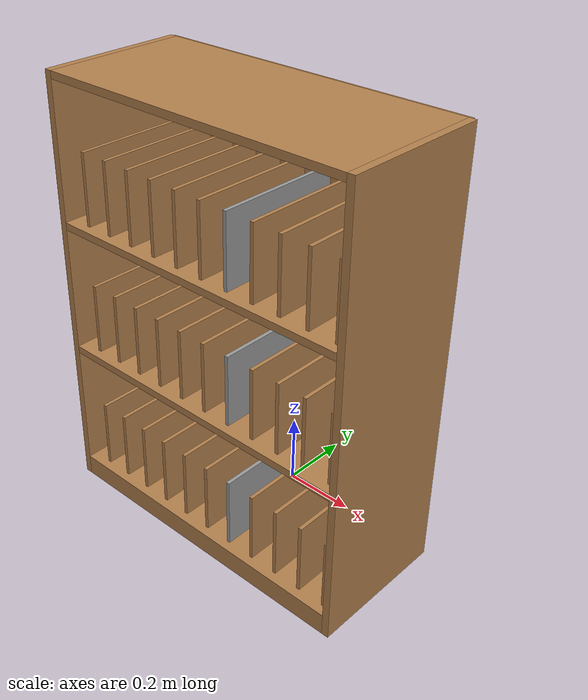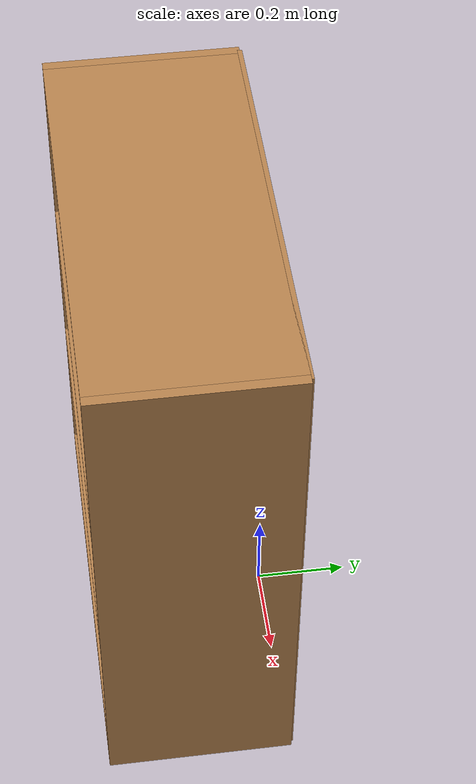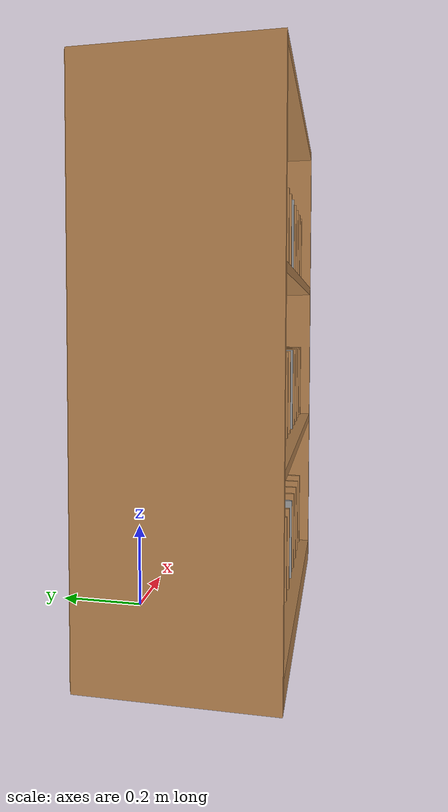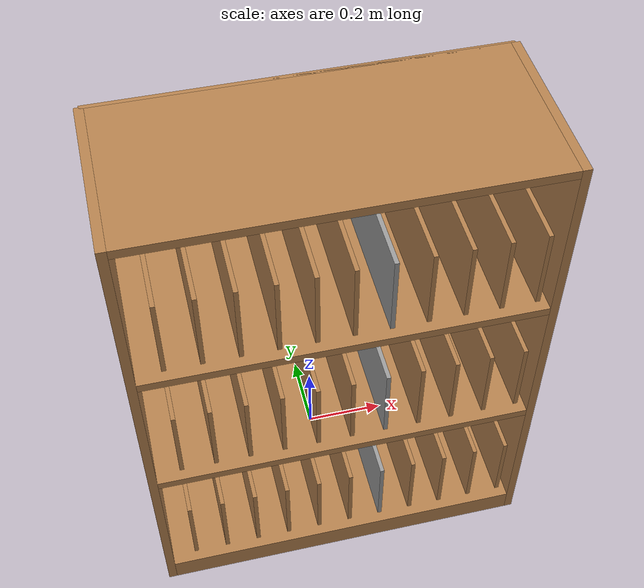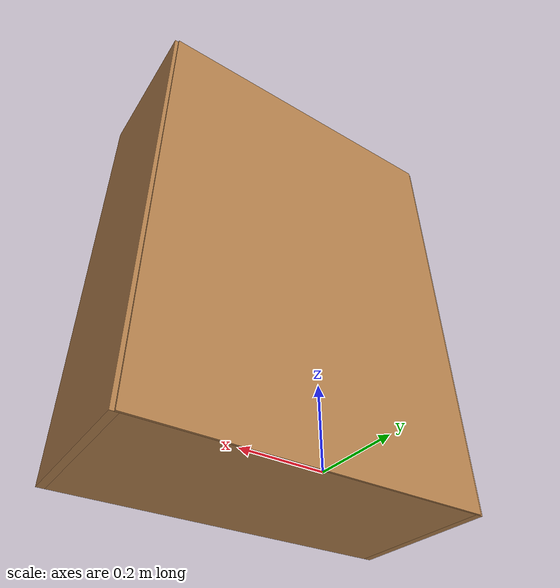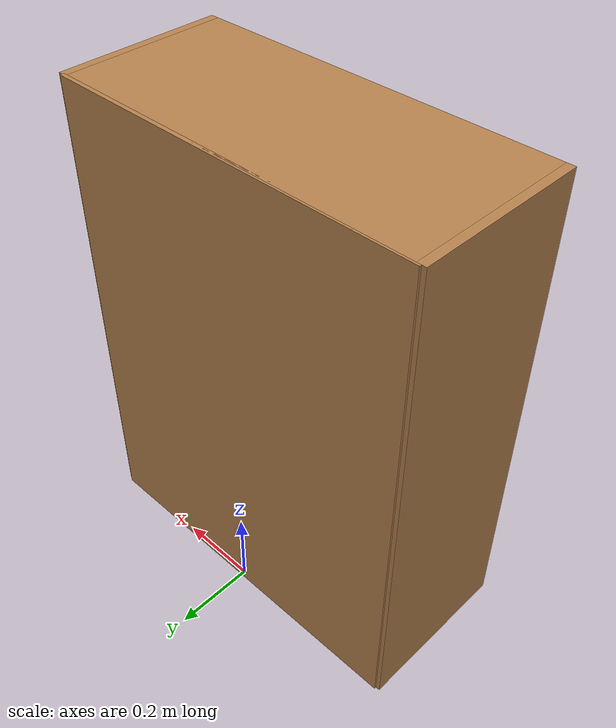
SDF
<?xml version='1.0'?>
<sdf version='1.7'>
  <model name='bookshelf'>
    <link name='link'>
      <inertial>
        <mass>1</mass>
      </inertial>
      <self_collide>0</self_collide>
      <enable_wind>0</enable_wind>
      <kinematic>0</kinematic>
      <pose>0 0 0 0 -0 0</pose>
      <visual name='visual1'>
        <pose>0 0.005 0.6 0 -0 0</pose>
        <geometry>
          <box>
            <size>0.9 0.01 1.2</size>
          </box>
        </geometry>
        <material>
          <script>
            <uri>file://media/materials/scripts/gazebo.material</uri>
            <name>Gazebo/Wood</name>
          </script>
          <shader type='pixel'/>
        </material>
        <transparency>0</transparency>
        <cast_shadows>1</cast_shadows>
      </visual>
      <visual name='visual7'>
        <pose>0 -0.195 0.8 0 -0 0</pose>
        <geometry>
          <box>
            <size>0.88 0.4 0.02</size>
          </box>
        </geometry>
        <material>
          <script>
            <uri>file://media/materials/scripts/gazebo.material</uri>
            <name>Gazebo/Wood</name>
          </script>
          <shader type='pixel'/>
        </material>
        <transparency>0</transparency>
        <cast_shadows>1</cast_shadows>
      </visual>
      <visual name='visual5'>
        <pose>0 -0.195 1.19 0 -0 0</pose>
        <geometry>
          <box>
            <size>0.88 0.4 0.02</size>
          </box>
        </geometry>
        <material>
          <script>
            <uri>file://media/materials/scripts/gazebo.material</uri>
            <name>Gazebo/Wood</name>
          </script>
          <shader type='pixel'/>
        </material>
        <transparency>0</transparency>
        <cast_shadows>1</cast_shadows>
      </visual>
      <visual name='visual6'>
        <pose>0 -0.195 0.43 0 -0 0</pose>
        <geometry>
          <box>
            <size>0.88 0.4 0.02</size>
          </box>
        </geometry>
        <material>
          <script>
            <uri>file://media/materials/scripts/gazebo.material</uri>
            <name>Gazebo/Wood</name>
          </script>
          <shader type='pixel'/>
        </material>
        <transparency>0</transparency>
        <cast_shadows>1</cast_shadows>
      </visual>
      <visual name='visual3'>
        <pose>-0.45 -0.195 0.6 0 -0 0</pose>
        <geometry>
          <box>
            <size>0.02 0.4 1.2</size>
          </box>
        </geometry>
        <material>
          <script>
            <uri>file://media/materials/scripts/gazebo.material</uri>
            <name>Gazebo/Wood</name>
          </script>
          <shader type='pixel'/>
        </material>
        <transparency>0</transparency>
        <cast_shadows>1</cast_shadows>
      </visual>
      <visual name='visual2'>
        <pose>0.45 -0.195 0.6 0 -0 0</pose>
        <geometry>
          <box>
            <size>0.02 0.4 1.2</size>
          </box>
        </geometry>
        <material>
          <script>
            <uri>file://media/materials/scripts/gazebo.material</uri>
            <name>Gazebo/Wood</name>
          </script>
          <shader type='pixel'/>
        </material>
        <transparency>0</transparency>
        <cast_shadows>1</cast_shadows>
      </visual>
      <visual name='visual4'>
        <pose>0 -0.195 0.03 0 -0 0</pose>
        <geometry>
          <box>
            <size>0.88 0.4 0.06</size>
          </box>
        </geometry>
        <material>
          <script>
            <uri>file://media/materials/scripts/gazebo.material</uri>
            <name>Gazebo/Wood</name>
          </script>
          <shader type='pixel'/>
        </material>
        <transparency>0</transparency>
        <cast_shadows>1</cast_shadows>
      </visual>
      <collision name='back'>
        <laser_retro>0</laser_retro>
        <max_contacts>10</max_contacts>
        <pose>0 0.005 0.6 0 -0 0</pose>
        <geometry>
          <box>
            <size>0.9 0.01 1.2</size>
          </box>
        </geometry>
        <surface>
          <friction>
            <ode>
              <mu>1</mu>
              <mu2>1</mu2>
              <fdir1>0 0 0</fdir1>
              <slip1>0</slip1>
              <slip2>0</slip2>
            </ode>
            <torsional>
              <coefficient>1</coefficient>
              <patch_radius>0</patch_radius>
              <surface_radius>0</surface_radius>
              <use_patch_radius>1</use_patch_radius>
              <ode>
                <slip>0</slip>
              </ode>
            </torsional>
          </friction>
          <bounce>
            <restitution_coefficient>0</restitution_coefficient>
            <threshold>1e+06</threshold>
          </bounce>
          <contact>
            <collide_without_contact>0</collide_without_contact>
            <collide_without_contact_bitmask>1</collide_without_contact_bitmask>
            <collide_bitmask>1</collide_bitmask>
            <ode>
              <soft_cfm>0</soft_cfm>
              <soft_erp>0.2</soft_erp>
              <kp>1e+13</kp>
              <kd>1</kd>
              <max_vel>0.01</max_vel>
              <min_depth>0</min_depth>
            </ode>
            <bullet>
              <split_impulse>1</split_impulse>
              <split_impulse_penetration_threshold>-0.01</split_impulse_penetration_threshold>
              <soft_cfm>0</soft_cfm>
              <soft_erp>0.2</soft_erp>
              <kp>1e+13</kp>
              <kd>1</kd>
            </bullet>
          </contact>
        </surface>
      </collision>
      <collision name='right_side'>
        <laser_retro>0</laser_retro>
        <max_contacts>10</max_contacts>
        <pose>-0.45 -0.195 0.6 0 -0 0</pose>
        <geometry>
          <box>
            <size>0.02 0.4 1.2</size>
          </box>
        </geometry>
        <surface>
          <friction>
            <ode>
              <mu>1</mu>
              <mu2>1</mu2>
              <fdir1>0 0 0</fdir1>
              <slip1>0</slip1>
              <slip2>0</slip2>
            </ode>
            <torsional>
              <coefficient>1</coefficient>
              <patch_radius>0</patch_radius>
              <surface_radius>0</surface_radius>
              <use_patch_radius>1</use_patch_radius>
              <ode>
                <slip>0</slip>
              </ode>
            </torsional>
          </friction>
          <bounce>
            <restitution_coefficient>0</restitution_coefficient>
            <threshold>1e+06</threshold>
          </bounce>
          <contact>
            <collide_without_contact>0</collide_without_contact>
            <collide_without_contact_bitmask>1</collide_without_contact_bitmask>
            <collide_bitmask>1</collide_bitmask>
            <ode>
              <soft_cfm>0</soft_cfm>
              <soft_erp>0.2</soft_erp>
              <kp>1e+13</kp>
              <kd>1</kd>
              <max_vel>0.01</max_vel>
              <min_depth>0</min_depth>
            </ode>
            <bullet>
              <split_impulse>1</split_impulse>
              <split_impulse_penetration_threshold>-0.01</split_impulse_penetration_threshold>
              <soft_cfm>0</soft_cfm>
              <soft_erp>0.2</soft_erp>
              <kp>1e+13</kp>
              <kd>1</kd>
            </bullet>
          </contact>
        </surface>
      </collision>
      <collision name='left_side'>
        <laser_retro>0</laser_retro>
        <max_contacts>10</max_contacts>
        <pose>0.45 -0.195 0.6 0 -0 0</pose>
        <geometry>
          <box>
            <size>0.02 0.4 1.2</size>
          </box>
        </geometry>
        <surface>
          <friction>
            <ode>
              <mu>1</mu>
              <mu2>1</mu2>
              <fdir1>0 0 0</fdir1>
              <slip1>0</slip1>
              <slip2>0</slip2>
            </ode>
            <torsional>
              <coefficient>1</coefficient>
              <patch_radius>0</patch_radius>
              <surface_radius>0</surface_radius>
              <use_patch_radius>1</use_patch_radius>
              <ode>
                <slip>0</slip>
              </ode>
            </torsional>
          </friction>
          <bounce>
            <restitution_coefficient>0</restitution_coefficient>
            <threshold>1e+06</threshold>
          </bounce>
          <contact>
            <collide_without_contact>0</collide_without_contact>
            <collide_without_contact_bitmask>1</collide_without_contact_bitmask>
            <collide_bitmask>1</collide_bitmask>
            <ode>
              <soft_cfm>0</soft_cfm>
              <soft_erp>0.2</soft_erp>
              <kp>1e+13</kp>
              <kd>1</kd>
              <max_vel>0.01</max_vel>
              <min_depth>0</min_depth>
            </ode>
            <bullet>
              <split_impulse>1</split_impulse>
              <split_impulse_penetration_threshold>-0.01</split_impulse_penetration_threshold>
              <soft_cfm>0</soft_cfm>
              <soft_erp>0.2</soft_erp>
              <kp>1e+13</kp>
              <kd>1</kd>
            </bullet>
          </contact>
        </surface>
      </collision>
      <collision name='high_shelf'>
        <laser_retro>0</laser_retro>
        <max_contacts>10</max_contacts>
        <pose>0 -0.195 0.8 0 -0 0</pose>
        <geometry>
          <box>
            <size>0.88 0.4 0.02</size>
          </box>
        </geometry>
        <surface>
          <friction>
            <ode>
              <mu>1</mu>
              <mu2>1</mu2>
              <fdir1>0 0 0</fdir1>
              <slip1>0</slip1>
              <slip2>0</slip2>
            </ode>
            <torsional>
              <coefficient>1</coefficient>
              <patch_radius>0</patch_radius>
              <surface_radius>0</surface_radius>
              <use_patch_radius>1</use_patch_radius>
              <ode>
                <slip>0</slip>
              </ode>
            </torsional>
          </friction>
          <bounce>
            <restitution_coefficient>0</restitution_coefficient>
            <threshold>1e+06</threshold>
          </bounce>
          <contact>
            <collide_without_contact>0</collide_without_contact>
            <collide_without_contact_bitmask>1</collide_without_contact_bitmask>
            <collide_bitmask>1</collide_bitmask>
            <ode>
              <soft_cfm>0</soft_cfm>
              <soft_erp>0.2</soft_erp>
              <kp>1e+13</kp>
              <kd>1</kd>
              <max_vel>0.01</max_vel>
              <min_depth>0</min_depth>
            </ode>
            <bullet>
              <split_impulse>1</split_impulse>
              <split_impulse_penetration_threshold>-0.01</split_impulse_penetration_threshold>
              <soft_cfm>0</soft_cfm>
              <soft_erp>0.2</soft_erp>
              <kp>1e+13</kp>
              <kd>1</kd>
            </bullet>
          </contact>
        </surface>
      </collision>
      <collision name='bottom'>
        <laser_retro>0</laser_retro>
        <max_contacts>10</max_contacts>
        <pose>0 -0.195 0.03 0 -0 0</pose>
        <geometry>
          <box>
            <size>0.88 0.4 0.06</size>
          </box>
        </geometry>
        <surface>
          <friction>
            <ode>
              <mu>1</mu>
              <mu2>1</mu2>
              <fdir1>0 0 0</fdir1>
              <slip1>0</slip1>
              <slip2>0</slip2>
            </ode>
            <torsional>
              <coefficient>1</coefficient>
              <patch_radius>0</patch_radius>
              <surface_radius>0</surface_radius>
              <use_patch_radius>1</use_patch_radius>
              <ode>
                <slip>0</slip>
              </ode>
            </torsional>
          </friction>
          <bounce>
            <restitution_coefficient>0</restitution_coefficient>
            <threshold>1e+06</threshold>
          </bounce>
          <contact>
            <collide_without_contact>0</collide_without_contact>
            <collide_without_contact_bitmask>1</collide_without_contact_bitmask>
            <collide_bitmask>1</collide_bitmask>
            <ode>
              <soft_cfm>0</soft_cfm>
              <soft_erp>0.2</soft_erp>
              <kp>1e+13</kp>
              <kd>1</kd>
              <max_vel>0.01</max_vel>
              <min_depth>0</min_depth>
            </ode>
            <bullet>
              <split_impulse>1</split_impulse>
              <split_impulse_penetration_threshold>-0.01</split_impulse_penetration_threshold>
              <soft_cfm>0</soft_cfm>
              <soft_erp>0.2</soft_erp>
              <kp>1e+13</kp>
              <kd>1</kd>
            </bullet>
          </contact>
        </surface>
      </collision>
      <collision name='top'>
        <laser_retro>0</laser_retro>
        <max_contacts>10</max_contacts>
        <pose>0 -0.195 1.19 0 -0 0</pose>
        <geometry>
          <box>
            <size>0.88 0.4 0.02</size>
          </box>
        </geometry>
        <surface>
          <friction>
            <ode>
              <mu>1</mu>
              <mu2>1</mu2>
              <fdir1>0 0 0</fdir1>
              <slip1>0</slip1>
              <slip2>0</slip2>
            </ode>
            <torsional>
              <coefficient>1</coefficient>
              <patch_radius>0</patch_radius>
              <surface_radius>0</surface_radius>
              <use_patch_radius>1</use_patch_radius>
              <ode>
                <slip>0</slip>
              </ode>
            </torsional>
          </friction>
          <bounce>
            <restitution_coefficient>0</restitution_coefficient>
            <threshold>1e+06</threshold>
          </bounce>
          <contact>
            <collide_without_contact>0</collide_without_contact>
            <collide_without_contact_bitmask>1</collide_without_contact_bitmask>
            <collide_bitmask>1</collide_bitmask>
            <ode>
              <soft_cfm>0</soft_cfm>
              <soft_erp>0.2</soft_erp>
              <kp>1e+13</kp>
              <kd>1</kd>
              <max_vel>0.01</max_vel>
              <min_depth>0</min_depth>
            </ode>
            <bullet>
              <split_impulse>1</split_impulse>
              <split_impulse_penetration_threshold>-0.01</split_impulse_penetration_threshold>
              <soft_cfm>0</soft_cfm>
              <soft_erp>0.2</soft_erp>
              <kp>1e+13</kp>
              <kd>1</kd>
            </bullet>
          </contact>
        </surface>
      </collision>
      <collision name='low_shelf'>
        <laser_retro>0</laser_retro>
        <max_contacts>10</max_contacts>
        <pose>0 -0.195 0.43 0 -0 0</pose>
        <geometry>
          <box>
            <size>0.88 0.4 0.02</size>
          </box>
        </geometry>
        <surface>
          <friction>
            <ode>
              <mu>1</mu>
              <mu2>1</mu2>
              <fdir1>0 0 0</fdir1>
              <slip1>0</slip1>
              <slip2>0</slip2>
            </ode>
            <torsional>
              <coefficient>1</coefficient>
              <patch_radius>0</patch_radius>
              <surface_radius>0</surface_radius>
              <use_patch_radius>1</use_patch_radius>
              <ode>
                <slip>0</slip>
              </ode>
            </torsional>
          </friction>
          <bounce>
            <restitution_coefficient>0</restitution_coefficient>
            <threshold>1e+06</threshold>
          </bounce>
          <contact>
            <collide_without_contact>0</collide_without_contact>
            <collide_without_contact_bitmask>1</collide_without_contact_bitmask>
            <collide_bitmask>1</collide_bitmask>
            <ode>
              <soft_cfm>0</soft_cfm>
              <soft_erp>0.2</soft_erp>
              <kp>1e+13</kp>
              <kd>1</kd>
              <max_vel>0.01</max_vel>
              <min_depth>0</min_depth>
            </ode>
            <bullet>
              <split_impulse>1</split_impulse>
              <split_impulse_penetration_threshold>-0.01</split_impulse_penetration_threshold>
              <soft_cfm>0</soft_cfm>
              <soft_erp>0.2</soft_erp>
              <kp>1e+13</kp>
              <kd>1</kd>
            </bullet>
          </contact>
        </surface>
      </collision>
    </link>
    <link name='link_1'>
      <inertial>
        <mass>1</mass>
        <inertia>
          <ixx>0.166667</ixx>
          <ixy>0</ixy>
          <ixz>0</ixz>
          <iyy>0.166667</iyy>
          <iyz>0</iyz>
          <izz>0.166667</izz>
        </inertia>
        <pose>0 0 0 0 -0 0</pose>
      </inertial>
      <pose>-0.38 -0.195 0.907998 0 0 -1.57</pose>
      <gravity>1</gravity>
      <self_collide>0</self_collide>
      <kinematic>0</kinematic>
      <enable_wind>0</enable_wind>
      <visual name='visual'>
        <pose>0 0 0 0 -0 0</pose>
        <geometry>
          <box>
            <size>0.35 0.01 0.2</size>
          </box>
        </geometry>
        <material>
          <script>
            <uri>file://media/materials/scripts/gazebo.material</uri>
            <name>Gazebo/Wood</name>
          </script>
          <shader type='pixel'/>
        </material>
        <transparency>0</transparency>
        <cast_shadows>1</cast_shadows>
      </visual>
      <visual name='ModelPreview_3::link_1::visual_1'>
        <pose>0 0 0 0 -0 0</pose>
        <geometry>
          <box>
            <size>0.35 0.01 0.2</size>
          </box>
        </geometry>
        <material>
          <lighting>1</lighting>
          <script>
            <uri>file://media/materials/scripts/gazebo.material</uri>
            <name>Gazebo/Grey</name>
          </script>
          <shader type='pixel'>
            <normal_map>__default__</normal_map>
          </shader>
          <ambient>0.3 0.3 0.3 1</ambient>
          <diffuse>0.7 0.7 0.7 1</diffuse>
          <specular>0.01 0.01 0.01 1</specular>
          <emissive>0 0 0 1</emissive>
        </material>
        <transparency>0</transparency>
        <cast_shadows>1</cast_shadows>
      </visual>
      <collision name='collision'>
        <laser_retro>0</laser_retro>
        <max_contacts>10</max_contacts>
        <pose>0 0 0 0 -0 0</pose>
        <geometry>
          <box>
            <size>0.35 0.01 0.2</size>
          </box>
        </geometry>
        <surface>
          <friction>
            <ode>
              <mu>1</mu>
              <mu2>1</mu2>
              <fdir1>0 0 0</fdir1>
              <slip1>0</slip1>
              <slip2>0</slip2>
            </ode>
            <torsional>
              <coefficient>1</coefficient>
              <patch_radius>0</patch_radius>
              <surface_radius>0</surface_radius>
              <use_patch_radius>1</use_patch_radius>
              <ode>
                <slip>0</slip>
              </ode>
            </torsional>
          </friction>
          <bounce>
            <restitution_coefficient>0</restitution_coefficient>
            <threshold>1e+06</threshold>
          </bounce>
          <contact>
            <collide_without_contact>0</collide_without_contact>
            <collide_without_contact_bitmask>1</collide_without_contact_bitmask>
            <collide_bitmask>1</collide_bitmask>
            <ode>
              <soft_cfm>0</soft_cfm>
              <soft_erp>0.2</soft_erp>
              <kp>1e+13</kp>
              <kd>1</kd>
              <max_vel>0.01</max_vel>
              <min_depth>0</min_depth>
            </ode>
            <bullet>
              <split_impulse>1</split_impulse>
              <split_impulse_penetration_threshold>-0.01</split_impulse_penetration_threshold>
              <soft_cfm>0</soft_cfm>
              <soft_erp>0.2</soft_erp>
              <kp>1e+13</kp>
              <kd>1</kd>
            </bullet>
          </contact>
        </surface>
      </collision>
    </link>
    <link name='link_2'>
      <inertial>
        <mass>1</mass>
        <inertia>
          <ixx>0.166667</ixx>
          <ixy>0</ixy>
          <ixz>0</ixz>
          <iyy>0.166667</iyy>
          <iyz>0</iyz>
          <izz>0.166667</izz>
        </inertia>
        <pose>0 0 0 0 -0 0</pose>
      </inertial>
      <pose>-0.3 -0.195 0.907998 0 0 -1.57</pose>
      <gravity>1</gravity>
      <self_collide>0</self_collide>
      <kinematic>0</kinematic>
      <enable_wind>0</enable_wind>
      <visual name='visual'>
        <pose>0 0 0 0 -0 0</pose>
        <geometry>
          <box>
            <size>0.35 0.01 0.2</size>
          </box>
        </geometry>
        <material>
          <script>
            <uri>file://media/materials/scripts/gazebo.material</uri>
            <name>Gazebo/Wood</name>
          </script>
          <shader type='pixel'/>
        </material>
        <transparency>0</transparency>
        <cast_shadows>1</cast_shadows>
      </visual>
      <visual name='ModelPreview_3::link_1::visual_1'>
        <pose>0 0 0 0 -0 0</pose>
        <geometry>
          <box>
            <size>0.35 0.01 0.2</size>
          </box>
        </geometry>
        <material>
          <lighting>1</lighting>
          <script>
            <uri>file://media/materials/scripts/gazebo.material</uri>
            <name>Gazebo/Grey</name>
          </script>
          <shader type='pixel'>
            <normal_map>__default__</normal_map>
          </shader>
          <ambient>0.3 0.3 0.3 1</ambient>
          <diffuse>0.7 0.7 0.7 1</diffuse>
          <specular>0.01 0.01 0.01 1</specular>
          <emissive>0 0 0 1</emissive>
        </material>
        <transparency>0</transparency>
        <cast_shadows>1</cast_shadows>
      </visual>
      <collision name='collision'>
        <laser_retro>0</laser_retro>
        <max_contacts>10</max_contacts>
        <pose>0 0 0 0 -0 0</pose>
        <geometry>
          <box>
            <size>0.35 0.01 0.2</size>
          </box>
        </geometry>
        <surface>
          <friction>
            <ode>
              <mu>1</mu>
              <mu2>1</mu2>
              <fdir1>0 0 0</fdir1>
              <slip1>0</slip1>
              <slip2>0</slip2>
            </ode>
            <torsional>
              <coefficient>1</coefficient>
              <patch_radius>0</patch_radius>
              <surface_radius>0</surface_radius>
              <use_patch_radius>1</use_patch_radius>
              <ode>
                <slip>0</slip>
              </ode>
            </torsional>
          </friction>
          <bounce>
            <restitution_coefficient>0</restitution_coefficient>
            <threshold>1e+06</threshold>
          </bounce>
          <contact>
            <collide_without_contact>0</collide_without_contact>
            <collide_without_contact_bitmask>1</collide_without_contact_bitmask>
            <collide_bitmask>1</collide_bitmask>
            <ode>
              <soft_cfm>0</soft_cfm>
              <soft_erp>0.2</soft_erp>
              <kp>1e+13</kp>
              <kd>1</kd>
              <max_vel>0.01</max_vel>
              <min_depth>0</min_depth>
            </ode>
            <bullet>
              <split_impulse>1</split_impulse>
              <split_impulse_penetration_threshold>-0.01</split_impulse_penetration_threshold>
              <soft_cfm>0</soft_cfm>
              <soft_erp>0.2</soft_erp>
              <kp>1e+13</kp>
              <kd>1</kd>
            </bullet>
          </contact>
        </surface>
      </collision>
    </link>
    <link name='link_3'>
      <inertial>
        <mass>1</mass>
        <inertia>
          <ixx>0.166667</ixx>
          <ixy>0</ixy>
          <ixz>0</ixz>
          <iyy>0.166667</iyy>
          <iyz>0</iyz>
          <izz>0.166667</izz>
        </inertia>
        <pose>0 0 0 0 -0 0</pose>
      </inertial>
      <pose>-0.22 -0.195 0.907998 0 0 -1.57</pose>
      <gravity>1</gravity>
      <self_collide>0</self_collide>
      <kinematic>0</kinematic>
      <enable_wind>0</enable_wind>
      <visual name='visual'>
        <pose>0 0 0 0 -0 0</pose>
        <geometry>
          <box>
            <size>0.35 0.01 0.2</size>
          </box>
        </geometry>
        <material>
          <script>
            <uri>file://media/materials/scripts/gazebo.material</uri>
            <name>Gazebo/Wood</name>
          </script>
          <shader type='pixel'/>
        </material>
        <transparency>0</transparency>
        <cast_shadows>1</cast_shadows>
      </visual>
      <visual name='ModelPreview_3::link_1::visual_1'>
        <pose>0 0 0 0 -0 0</pose>
        <geometry>
          <box>
            <size>0.35 0.01 0.2</size>
          </box>
        </geometry>
        <material>
          <lighting>1</lighting>
          <script>
            <uri>file://media/materials/scripts/gazebo.material</uri>
            <name>Gazebo/Grey</name>
          </script>
          <shader type='pixel'>
            <normal_map>__default__</normal_map>
          </shader>
          <ambient>0.3 0.3 0.3 1</ambient>
          <diffuse>0.7 0.7 0.7 1</diffuse>
          <specular>0.01 0.01 0.01 1</specular>
          <emissive>0 0 0 1</emissive>
        </material>
        <transparency>0</transparency>
        <cast_shadows>1</cast_shadows>
      </visual>
      <collision name='collision'>
        <laser_retro>0</laser_retro>
        <max_contacts>10</max_contacts>
        <pose>0 0 0 0 -0 0</pose>
        <geometry>
          <box>
            <size>0.35 0.01 0.2</size>
          </box>
        </geometry>
        <surface>
          <friction>
            <ode>
              <mu>1</mu>
              <mu2>1</mu2>
              <fdir1>0 0 0</fdir1>
              <slip1>0</slip1>
              <slip2>0</slip2>
            </ode>
            <torsional>
              <coefficient>1</coefficient>
              <patch_radius>0</patch_radius>
              <surface_radius>0</surface_radius>
              <use_patch_radius>1</use_patch_radius>
              <ode>
                <slip>0</slip>
              </ode>
            </torsional>
          </friction>
          <bounce>
            <restitution_coefficient>0</restitution_coefficient>
            <threshold>1e+06</threshold>
          </bounce>
          <contact>
            <collide_without_contact>0</collide_without_contact>
            <collide_without_contact_bitmask>1</collide_without_contact_bitmask>
            <collide_bitmask>1</collide_bitmask>
            <ode>
              <soft_cfm>0</soft_cfm>
              <soft_erp>0.2</soft_erp>
              <kp>1e+13</kp>
              <kd>1</kd>
              <max_vel>0.01</max_vel>
              <min_depth>0</min_depth>
            </ode>
            <bullet>
              <split_impulse>1</split_impulse>
              <split_impulse_penetration_threshold>-0.01</split_impulse_penetration_threshold>
              <soft_cfm>0</soft_cfm>
              <soft_erp>0.2</soft_erp>
              <kp>1e+13</kp>
              <kd>1</kd>
            </bullet>
          </contact>
        </surface>
      </collision>
    </link>
    <link name='link_4'>
      <inertial>
        <mass>1</mass>
        <inertia>
          <ixx>0.166667</ixx>
          <ixy>0</ixy>
          <ixz>0</ixz>
          <iyy>0.166667</iyy>
          <iyz>0</iyz>
          <izz>0.166667</izz>
        </inertia>
        <pose>0 0 0 0 -0 0</pose>
      </inertial>
      <pose>-0.14 -0.195 0.907998 0 0 -1.57</pose>
      <gravity>1</gravity>
      <self_collide>0</self_collide>
      <kinematic>0</kinematic>
      <enable_wind>0</enable_wind>
      <visual name='visual'>
        <pose>0 0 0 0 -0 0</pose>
        <geometry>
          <box>
            <size>0.35 0.01 0.2</size>
          </box>
        </geometry>
        <material>
          <script>
            <uri>file://media/materials/scripts/gazebo.material</uri>
            <name>Gazebo/Wood</name>
          </script>
          <shader type='pixel'/>
        </material>
        <transparency>0</transparency>
        <cast_shadows>1</cast_shadows>
      </visual>
      <visual name='ModelPreview_3::link_1::visual_1'>
        <pose>0 0 0 0 -0 0</pose>
        <geometry>
          <box>
            <size>0.35 0.01 0.2</size>
          </box>
        </geometry>
        <material>
          <lighting>1</lighting>
          <script>
            <uri>file://media/materials/scripts/gazebo.material</uri>
            <name>Gazebo/Grey</name>
          </script>
          <shader type='pixel'>
            <normal_map>__default__</normal_map>
          </shader>
          <ambient>0.3 0.3 0.3 1</ambient>
          <diffuse>0.7 0.7 0.7 1</diffuse>
          <specular>0.01 0.01 0.01 1</specular>
          <emissive>0 0 0 1</emissive>
        </material>
        <transparency>0</transparency>
        <cast_shadows>1</cast_shadows>
      </visual>
      <collision name='collision'>
        <laser_retro>0</laser_retro>
        <max_contacts>10</max_contacts>
        <pose>0 0 0 0 -0 0</pose>
        <geometry>
          <box>
            <size>0.35 0.01 0.2</size>
          </box>
        </geometry>
        <surface>
          <friction>
            <ode>
              <mu>1</mu>
              <mu2>1</mu2>
              <fdir1>0 0 0</fdir1>
              <slip1>0</slip1>
              <slip2>0</slip2>
            </ode>
            <torsional>
              <coefficient>1</coefficient>
              <patch_radius>0</patch_radius>
              <surface_radius>0</surface_radius>
              <use_patch_radius>1</use_patch_radius>
              <ode>
                <slip>0</slip>
              </ode>
            </torsional>
          </friction>
          <bounce>
            <restitution_coefficient>0</restitution_coefficient>
            <threshold>1e+06</threshold>
          </bounce>
          <contact>
            <collide_without_contact>0</collide_without_contact>
            <collide_without_contact_bitmask>1</collide_without_contact_bitmask>
            <collide_bitmask>1</collide_bitmask>
            <ode>
              <soft_cfm>0</soft_cfm>
              <soft_erp>0.2</soft_erp>
              <kp>1e+13</kp>
              <kd>1</kd>
              <max_vel>0.01</max_vel>
              <min_depth>0</min_depth>
            </ode>
            <bullet>
              <split_impulse>1</split_impulse>
              <split_impulse_penetration_threshold>-0.01</split_impulse_penetration_threshold>
              <soft_cfm>0</soft_cfm>
              <soft_erp>0.2</soft_erp>
              <kp>1e+13</kp>
              <kd>1</kd>
            </bullet>
          </contact>
        </surface>
      </collision>
    </link>
    <link name='link_5'>
      <inertial>
        <mass>1</mass>
        <inertia>
          <ixx>0.166667</ixx>
          <ixy>0</ixy>
          <ixz>0</ixz>
          <iyy>0.166667</iyy>
          <iyz>0</iyz>
          <izz>0.166667</izz>
        </inertia>
        <pose>0 0 0 0 -0 0</pose>
      </inertial>
      <pose>-0.06 -0.195 0.907998 0 0 -1.57</pose>
      <gravity>1</gravity>
      <self_collide>0</self_collide>
      <kinematic>0</kinematic>
      <enable_wind>0</enable_wind>
      <visual name='visual'>
        <pose>0 0 0 0 -0 0</pose>
        <geometry>
          <box>
            <size>0.35 0.01 0.2</size>
          </box>
        </geometry>
        <material>
          <script>
            <uri>file://media/materials/scripts/gazebo.material</uri>
            <name>Gazebo/Wood</name>
          </script>
          <shader type='pixel'/>
        </material>
        <transparency>0</transparency>
        <cast_shadows>1</cast_shadows>
      </visual>
      <visual name='ModelPreview_3::link_1::visual_1'>
        <pose>0 0 0 0 -0 0</pose>
        <geometry>
          <box>
            <size>0.35 0.01 0.2</size>
          </box>
        </geometry>
        <material>
          <lighting>1</lighting>
          <script>
            <uri>file://media/materials/scripts/gazebo.material</uri>
            <name>Gazebo/Grey</name>
          </script>
          <shader type='pixel'>
            <normal_map>__default__</normal_map>
          </shader>
          <ambient>0.3 0.3 0.3 1</ambient>
          <diffuse>0.7 0.7 0.7 1</diffuse>
          <specular>0.01 0.01 0.01 1</specular>
          <emissive>0 0 0 1</emissive>
        </material>
        <transparency>0</transparency>
        <cast_shadows>1</cast_shadows>
      </visual>
      <collision name='collision'>
        <laser_retro>0</laser_retro>
        <max_contacts>10</max_contacts>
        <pose>0 0 0 0 -0 0</pose>
        <geometry>
          <box>
            <size>0.35 0.01 0.2</size>
          </box>
        </geometry>
        <surface>
          <friction>
            <ode>
              <mu>1</mu>
              <mu2>1</mu2>
              <fdir1>0 0 0</fdir1>
              <slip1>0</slip1>
              <slip2>0</slip2>
            </ode>
            <torsional>
              <coefficient>1</coefficient>
              <patch_radius>0</patch_radius>
              <surface_radius>0</surface_radius>
              <use_patch_radius>1</use_patch_radius>
              <ode>
                <slip>0</slip>
              </ode>
            </torsional>
          </friction>
          <bounce>
            <restitution_coefficient>0</restitution_coefficient>
            <threshold>1e+06</threshold>
          </bounce>
          <contact>
            <collide_without_contact>0</collide_without_contact>
            <collide_without_contact_bitmask>1</collide_without_contact_bitmask>
            <collide_bitmask>1</collide_bitmask>
            <ode>
              <soft_cfm>0</soft_cfm>
              <soft_erp>0.2</soft_erp>
              <kp>1e+13</kp>
              <kd>1</kd>
              <max_vel>0.01</max_vel>
              <min_depth>0</min_depth>
            </ode>
            <bullet>
              <split_impulse>1</split_impulse>
              <split_impulse_penetration_threshold>-0.01</split_impulse_penetration_threshold>
              <soft_cfm>0</soft_cfm>
              <soft_erp>0.2</soft_erp>
              <kp>1e+13</kp>
              <kd>1</kd>
            </bullet>
          </contact>
        </surface>
      </collision>
    </link>
    <link name='link_6'>
      <inertial>
        <mass>1</mass>
        <inertia>
          <ixx>0.166667</ixx>
          <ixy>0</ixy>
          <ixz>0</ixz>
          <iyy>0.166667</iyy>
          <iyz>0</iyz>
          <izz>0.166667</izz>
        </inertia>
        <pose>0 0 0 0 -0 0</pose>
      </inertial>
      <pose>0.02 -0.195 0.907998 0 0 -1.57</pose>
      <gravity>1</gravity>
      <self_collide>0</self_collide>
      <kinematic>0</kinematic>
      <enable_wind>0</enable_wind>
      <visual name='visual'>
        <pose>0 0 0 0 -0 0</pose>
        <geometry>
          <box>
            <size>0.35 0.01 0.2</size>
          </box>
        </geometry>
        <material>
          <script>
            <uri>file://media/materials/scripts/gazebo.material</uri>
            <name>Gazebo/Wood</name>
          </script>
          <shader type='pixel'/>
        </material>
        <transparency>0</transparency>
        <cast_shadows>1</cast_shadows>
      </visual>
      <visual name='ModelPreview_3::link_1::visual_1'>
        <pose>0 0 0 0 -0 0</pose>
        <geometry>
          <box>
            <size>0.35 0.01 0.2</size>
          </box>
        </geometry>
        <material>
          <lighting>1</lighting>
          <script>
            <uri>file://media/materials/scripts/gazebo.material</uri>
            <name>Gazebo/Grey</name>
          </script>
          <shader type='pixel'>
            <normal_map>__default__</normal_map>
          </shader>
          <ambient>0.3 0.3 0.3 1</ambient>
          <diffuse>0.7 0.7 0.7 1</diffuse>
          <specular>0.01 0.01 0.01 1</specular>
          <emissive>0 0 0 1</emissive>
        </material>
        <transparency>0</transparency>
        <cast_shadows>1</cast_shadows>
      </visual>
      <collision name='collision'>
        <laser_retro>0</laser_retro>
        <max_contacts>10</max_contacts>
        <pose>0 0 0 0 -0 0</pose>
        <geometry>
          <box>
            <size>0.35 0.01 0.2</size>
          </box>
        </geometry>
        <surface>
          <friction>
            <ode>
              <mu>1</mu>
              <mu2>1</mu2>
              <fdir1>0 0 0</fdir1>
              <slip1>0</slip1>
              <slip2>0</slip2>
            </ode>
            <torsional>
              <coefficient>1</coefficient>
              <patch_radius>0</patch_radius>
              <surface_radius>0</surface_radius>
              <use_patch_radius>1</use_patch_radius>
              <ode>
                <slip>0</slip>
              </ode>
            </torsional>
          </friction>
          <bounce>
            <restitution_coefficient>0</restitution_coefficient>
            <threshold>1e+06</threshold>
          </bounce>
          <contact>
            <collide_without_contact>0</collide_without_contact>
            <collide_without_contact_bitmask>1</collide_without_contact_bitmask>
            <collide_bitmask>1</collide_bitmask>
            <ode>
              <soft_cfm>0</soft_cfm>
              <soft_erp>0.2</soft_erp>
              <kp>1e+13</kp>
              <kd>1</kd>
              <max_vel>0.01</max_vel>
              <min_depth>0</min_depth>
            </ode>
            <bullet>
              <split_impulse>1</split_impulse>
              <split_impulse_penetration_threshold>-0.01</split_impulse_penetration_threshold>
              <soft_cfm>0</soft_cfm>
              <soft_erp>0.2</soft_erp>
              <kp>1e+13</kp>
              <kd>1</kd>
            </bullet>
          </contact>
        </surface>
      </collision>
    </link>
    <link name='link_7'>
      <inertial>
        <mass>1</mass>
        <inertia>
          <ixx>0.166667</ixx>
          <ixy>0</ixy>
          <ixz>0</ixz>
          <iyy>0.166667</iyy>
          <iyz>0</iyz>
          <izz>0.166667</izz>
        </inertia>
        <pose>0 0 0 0 -0 0</pose>
      </inertial>
      <pose>0.1 -0.195 0.907998 0 0 -1.57</pose>
      <gravity>1</gravity>
      <self_collide>0</self_collide>
      <kinematic>0</kinematic>
      <enable_wind>0</enable_wind>
      <visual name='visual'>
        <pose>0 0 0 0 -0 0</pose>
        <geometry>
          <box>
            <size>0.35 0.01 0.2</size>
          </box>
        </geometry>
        <material>
          <lighting>1</lighting>
          <script>
            <uri>file://media/materials/scripts/gazebo.material</uri>
            <name>Gazebo/Grey</name>
          </script>
          <shader type='pixel'>
            <normal_map>__default__</normal_map>
          </shader>
          <ambient>0.3 0.3 0.3 1</ambient>
          <diffuse>0.7 0.7 0.7 1</diffuse>
          <specular>0.01 0.01 0.01 1</specular>
          <emissive>0 0 0 1</emissive>
        </material>
        <transparency>0</transparency>
        <cast_shadows>1</cast_shadows>
      </visual>
      <visual name='ModelPreview_3::link_1::visual_1'>
        <pose>0 0 0 0 -0 0</pose>
        <geometry>
          <box>
            <size>0.35 0.01 0.2</size>
          </box>
        </geometry>
        <material>
          <script>
            <uri>file://media/materials/scripts/gazebo.material</uri>
            <name>Gazebo/Wood</name>
          </script>
          <shader type='pixel'/>
        </material>
        <transparency>0</transparency>
        <cast_shadows>1</cast_shadows>
      </visual>
      <collision name='collision'>
        <laser_retro>0</laser_retro>
        <max_contacts>10</max_contacts>
        <pose>0 0 0 0 -0 0</pose>
        <geometry>
          <box>
            <size>0.35 0.01 0.2</size>
          </box>
        </geometry>
        <surface>
          <friction>
            <ode>
              <mu>1</mu>
              <mu2>1</mu2>
              <fdir1>0 0 0</fdir1>
              <slip1>0</slip1>
              <slip2>0</slip2>
            </ode>
            <torsional>
              <coefficient>1</coefficient>
              <patch_radius>0</patch_radius>
              <surface_radius>0</surface_radius>
              <use_patch_radius>1</use_patch_radius>
              <ode>
                <slip>0</slip>
              </ode>
            </torsional>
          </friction>
          <bounce>
            <restitution_coefficient>0</restitution_coefficient>
            <threshold>1e+06</threshold>
          </bounce>
          <contact>
            <collide_without_contact>0</collide_without_contact>
            <collide_without_contact_bitmask>1</collide_without_contact_bitmask>
            <collide_bitmask>1</collide_bitmask>
            <ode>
              <soft_cfm>0</soft_cfm>
              <soft_erp>0.2</soft_erp>
              <kp>1e+13</kp>
              <kd>1</kd>
              <max_vel>0.01</max_vel>
              <min_depth>0</min_depth>
            </ode>
            <bullet>
              <split_impulse>1</split_impulse>
              <split_impulse_penetration_threshold>-0.01</split_impulse_penetration_threshold>
              <soft_cfm>0</soft_cfm>
              <soft_erp>0.2</soft_erp>
              <kp>1e+13</kp>
              <kd>1</kd>
            </bullet>
          </contact>
        </surface>
      </collision>
    </link>
    <link name='link_8'>
      <inertial>
        <mass>1</mass>
        <inertia>
          <ixx>0.166667</ixx>
          <ixy>0</ixy>
          <ixz>0</ixz>
          <iyy>0.166667</iyy>
          <iyz>0</iyz>
          <izz>0.166667</izz>
        </inertia>
        <pose>0 0 0 0 -0 0</pose>
      </inertial>
      <pose>0.18 -0.195 0.907998 0 0 -1.57</pose>
      <gravity>1</gravity>
      <self_collide>0</self_collide>
      <kinematic>0</kinematic>
      <enable_wind>0</enable_wind>
      <visual name='visual'>
        <pose>0 0 0 0 -0 0</pose>
        <geometry>
          <box>
            <size>0.35 0.01 0.2</size>
          </box>
        </geometry>
        <material>
          <script>
            <uri>file://media/materials/scripts/gazebo.material</uri>
            <name>Gazebo/Wood</name>
          </script>
          <shader type='pixel'/>
        </material>
        <transparency>0</transparency>
        <cast_shadows>1</cast_shadows>
      </visual>
      <visual name='ModelPreview_3::link_1::visual_1'>
        <pose>0 0 0 0 -0 0</pose>
        <geometry>
          <box>
            <size>0.35 0.01 0.2</size>
          </box>
        </geometry>
        <material>
          <lighting>1</lighting>
          <script>
            <uri>file://media/materials/scripts/gazebo.material</uri>
            <name>Gazebo/Grey</name>
          </script>
          <shader type='pixel'>
            <normal_map>__default__</normal_map>
          </shader>
          <ambient>0.3 0.3 0.3 1</ambient>
          <diffuse>0.7 0.7 0.7 1</diffuse>
          <specular>0.01 0.01 0.01 1</specular>
          <emissive>0 0 0 1</emissive>
        </material>
        <transparency>0</transparency>
        <cast_shadows>1</cast_shadows>
      </visual>
      <collision name='collision'>
        <laser_retro>0</laser_retro>
        <max_contacts>10</max_contacts>
        <pose>0 0 0 0 -0 0</pose>
        <geometry>
          <box>
            <size>0.35 0.01 0.2</size>
          </box>
        </geometry>
        <surface>
          <friction>
            <ode>
              <mu>1</mu>
              <mu2>1</mu2>
              <fdir1>0 0 0</fdir1>
              <slip1>0</slip1>
              <slip2>0</slip2>
            </ode>
            <torsional>
              <coefficient>1</coefficient>
              <patch_radius>0</patch_radius>
              <surface_radius>0</surface_radius>
              <use_patch_radius>1</use_patch_radius>
              <ode>
                <slip>0</slip>
              </ode>
            </torsional>
          </friction>
          <bounce>
            <restitution_coefficient>0</restitution_coefficient>
            <threshold>1e+06</threshold>
          </bounce>
          <contact>
            <collide_without_contact>0</collide_without_contact>
            <collide_without_contact_bitmask>1</collide_without_contact_bitmask>
            <collide_bitmask>1</collide_bitmask>
            <ode>
              <soft_cfm>0</soft_cfm>
              <soft_erp>0.2</soft_erp>
              <kp>1e+13</kp>
              <kd>1</kd>
              <max_vel>0.01</max_vel>
              <min_depth>0</min_depth>
            </ode>
            <bullet>
              <split_impulse>1</split_impulse>
              <split_impulse_penetration_threshold>-0.01</split_impulse_penetration_threshold>
              <soft_cfm>0</soft_cfm>
              <soft_erp>0.2</soft_erp>
              <kp>1e+13</kp>
              <kd>1</kd>
            </bullet>
          </contact>
        </surface>
      </collision>
    </link>
    <link name='link_9'>
      <inertial>
        <mass>1</mass>
        <inertia>
          <ixx>0.166667</ixx>
          <ixy>0</ixy>
          <ixz>0</ixz>
          <iyy>0.166667</iyy>
          <iyz>0</iyz>
          <izz>0.166667</izz>
        </inertia>
        <pose>0 0 0 0 -0 0</pose>
      </inertial>
      <pose>0.26 -0.195 0.907998 0 0 -1.57</pose>
      <gravity>1</gravity>
      <self_collide>0</self_collide>
      <kinematic>0</kinematic>
      <enable_wind>0</enable_wind>
      <visual name='ModelPreview_3::link_1::visual_1'>
        <pose>0 0 0 0 -0 0</pose>
        <geometry>
          <box>
            <size>0.35 0.01 0.2</size>
          </box>
        </geometry>
        <material>
          <script>
            <uri>file://media/materials/scripts/gazebo.material</uri>
            <name>Gazebo/Wood</name>
          </script>
          <shader type='pixel'/>
        </material>
        <transparency>0</transparency>
        <cast_shadows>1</cast_shadows>
      </visual>
      <visual name='visual'>
        <pose>0 0 0 0 -0 0</pose>
        <geometry>
          <box>
            <size>0.35 0.01 0.2</size>
          </box>
        </geometry>
        <material>
          <lighting>1</lighting>
          <script>
            <uri>file://media/materials/scripts/gazebo.material</uri>
            <name>Gazebo/Grey</name>
          </script>
          <shader type='pixel'>
            <normal_map>__default__</normal_map>
          </shader>
          <ambient>0.3 0.3 0.3 1</ambient>
          <diffuse>0.7 0.7 0.7 1</diffuse>
          <specular>0.01 0.01 0.01 1</specular>
          <emissive>0 0 0 1</emissive>
        </material>
        <transparency>0</transparency>
        <cast_shadows>1</cast_shadows>
      </visual>
      <collision name='collision'>
        <laser_retro>0</laser_retro>
        <max_contacts>10</max_contacts>
        <pose>0 0 0 0 -0 0</pose>
        <geometry>
          <box>
            <size>0.35 0.01 0.2</size>
          </box>
        </geometry>
        <surface>
          <friction>
            <ode>
              <mu>1</mu>
              <mu2>1</mu2>
              <fdir1>0 0 0</fdir1>
              <slip1>0</slip1>
              <slip2>0</slip2>
            </ode>
            <torsional>
              <coefficient>1</coefficient>
              <patch_radius>0</patch_radius>
              <surface_radius>0</surface_radius>
              <use_patch_radius>1</use_patch_radius>
              <ode>
                <slip>0</slip>
              </ode>
            </torsional>
          </friction>
          <bounce>
            <restitution_coefficient>0</restitution_coefficient>
            <threshold>1e+06</threshold>
          </bounce>
          <contact>
            <collide_without_contact>0</collide_without_contact>
            <collide_without_contact_bitmask>1</collide_without_contact_bitmask>
            <collide_bitmask>1</collide_bitmask>
            <ode>
              <soft_cfm>0</soft_cfm>
              <soft_erp>0.2</soft_erp>
              <kp>1e+13</kp>
              <kd>1</kd>
              <max_vel>0.01</max_vel>
              <min_depth>0</min_depth>
            </ode>
            <bullet>
              <split_impulse>1</split_impulse>
              <split_impulse_penetration_threshold>-0.01</split_impulse_penetration_threshold>
              <soft_cfm>0</soft_cfm>
              <soft_erp>0.2</soft_erp>
              <kp>1e+13</kp>
              <kd>1</kd>
            </bullet>
          </contact>
        </surface>
      </collision>
    </link>

    <link name='link_10'>
      <inertial>
        <mass>1</mass>
        <inertia>
          <ixx>0.166667</ixx>
          <ixy>0</ixy>
          <ixz>0</ixz>
          <iyy>0.166667</iyy>
          <iyz>0</iyz>
          <izz>0.166667</izz>
        </inertia>
        <pose>0 0 0 0 -0 0</pose>
      </inertial>
      <pose>0.34 -0.195 0.907998 0 0 -1.57</pose>
      <gravity>1</gravity>
      <self_collide>0</self_collide>
      <kinematic>0</kinematic>
      <enable_wind>0</enable_wind>
      <visual name='ModelPreview_3::link_1::visual_1'>
        <pose>0 0 0 0 -0 0</pose>
        <geometry>
          <box>
            <size>0.35 0.01 0.2</size>
          </box>
        </geometry>
        <material>
          <script>
            <uri>file://media/materials/scripts/gazebo.material</uri>
            <name>Gazebo/Wood</name>
          </script>
          <shader type='pixel'/>
        </material>
        <transparency>0</transparency>
        <cast_shadows>1</cast_shadows>
      </visual>
      <visual name='visual'>
        <pose>0 0 0 0 -0 0</pose>
        <geometry>
          <box>
            <size>0.35 0.01 0.2</size>
          </box>
        </geometry>
        <material>
          <lighting>1</lighting>
          <script>
            <uri>file://media/materials/scripts/gazebo.material</uri>
            <name>Gazebo/Grey</name>
          </script>
          <shader type='pixel'>
            <normal_map>__default__</normal_map>
          </shader>
          <ambient>0.3 0.3 0.3 1</ambient>
          <diffuse>0.7 0.7 0.7 1</diffuse>
          <specular>0.01 0.01 0.01 1</specular>
          <emissive>0 0 0 1</emissive>
        </material>
        <transparency>0</transparency>
        <cast_shadows>1</cast_shadows>
      </visual>
      <collision name='collision'>
        <laser_retro>0</laser_retro>
        <max_contacts>10</max_contacts>
        <pose>0 0 0 0 -0 0</pose>
        <geometry>
          <box>
            <size>0.35 0.01 0.2</size>
          </box>
        </geometry>
        <surface>
          <friction>
            <ode>
              <mu>1</mu>
              <mu2>1</mu2>
              <fdir1>0 0 0</fdir1>
              <slip1>0</slip1>
              <slip2>0</slip2>
            </ode>
            <torsional>
              <coefficient>1</coefficient>
              <patch_radius>0</patch_radius>
              <surface_radius>0</surface_radius>
              <use_patch_radius>1</use_patch_radius>
              <ode>
                <slip>0</slip>
              </ode>
            </torsional>
          </friction>
          <bounce>
            <restitution_coefficient>0</restitution_coefficient>
            <threshold>1e+06</threshold>
          </bounce>
          <contact>
            <collide_without_contact>0</collide_without_contact>
            <collide_without_contact_bitmask>1</collide_without_contact_bitmask>
            <collide_bitmask>1</collide_bitmask>
            <ode>
              <soft_cfm>0</soft_cfm>
              <soft_erp>0.2</soft_erp>
              <kp>1e+13</kp>
              <kd>1</kd>
              <max_vel>0.01</max_vel>
              <min_depth>0</min_depth>
            </ode>
            <bullet>
              <split_impulse>1</split_impulse>
              <split_impulse_penetration_threshold>-0.01</split_impulse_penetration_threshold>
              <soft_cfm>0</soft_cfm>
              <soft_erp>0.2</soft_erp>
              <kp>1e+13</kp>
              <kd>1</kd>
            </bullet>
          </contact>
        </surface>
      </collision>
    </link>

    <link name='link_11'>
      <inertial>
        <mass>1</mass>
        <inertia>
          <ixx>0.166667</ixx>
          <ixy>0</ixy>
          <ixz>0</ixz>
          <iyy>0.166667</iyy>
          <iyz>0</iyz>
          <izz>0.166667</izz>
        </inertia>
        <pose>0 0 0 0 -0 0</pose>
      </inertial>
      <pose>0.42 -0.195 0.907998 0 0 -1.57</pose>
      <gravity>1</gravity>
      <self_collide>0</self_collide>
      <kinematic>0</kinematic>
      <enable_wind>0</enable_wind>
      <visual name='ModelPreview_3::link_1::visual_1'>
        <pose>0 0 0 0 -0 0</pose>
        <geometry>
          <box>
            <size>0.35 0.01 0.2</size>
          </box>
        </geometry>
        <material>
          <script>
            <uri>file://media/materials/scripts/gazebo.material</uri>
            <name>Gazebo/Wood</name>
          </script>
          <shader type='pixel'/>
        </material>
        <transparency>0</transparency>
        <cast_shadows>1</cast_shadows>
      </visual>
      <visual name='visual'>
        <pose>0 0 0 0 -0 0</pose>
        <geometry>
          <box>
            <size>0.35 0.01 0.2</size>
          </box>
        </geometry>
        <material>
          <lighting>1</lighting>
          <script>
            <uri>file://media/materials/scripts/gazebo.material</uri>
            <name>Gazebo/Grey</name>
          </script>
          <shader type='pixel'>
            <normal_map>__default__</normal_map>
          </shader>
          <ambient>0.3 0.3 0.3 1</ambient>
          <diffuse>0.7 0.7 0.7 1</diffuse>
          <specular>0.01 0.01 0.01 1</specular>
          <emissive>0 0 0 1</emissive>
        </material>
        <transparency>0</transparency>
        <cast_shadows>1</cast_shadows>
      </visual>
      <collision name='collision'>
        <laser_retro>0</laser_retro>
        <max_contacts>10</max_contacts>
        <pose>0 0 0 0 -0 0</pose>
        <geometry>
          <box>
            <size>0.35 0.01 0.2</size>
          </box>
        </geometry>
        <surface>
          <friction>
            <ode>
              <mu>1</mu>
              <mu2>1</mu2>
              <fdir1>0 0 0</fdir1>
              <slip1>0</slip1>
              <slip2>0</slip2>
            </ode>
            <torsional>
              <coefficient>1</coefficient>
              <patch_radius>0</patch_radius>
              <surface_radius>0</surface_radius>
              <use_patch_radius>1</use_patch_radius>
              <ode>
                <slip>0</slip>
              </ode>
            </torsional>
          </friction>
          <bounce>
            <restitution_coefficient>0</restitution_coefficient>
            <threshold>1e+06</threshold>
          </bounce>
          <contact>
            <collide_without_contact>0</collide_without_contact>
            <collide_without_contact_bitmask>1</collide_without_contact_bitmask>
            <collide_bitmask>1</collide_bitmask>
            <ode>
              <soft_cfm>0</soft_cfm>
              <soft_erp>0.2</soft_erp>
              <kp>1e+13</kp>
              <kd>1</kd>
              <max_vel>0.01</max_vel>
              <min_depth>0</min_depth>
            </ode>
            <bullet>
              <split_impulse>1</split_impulse>
              <split_impulse_penetration_threshold>-0.01</split_impulse_penetration_threshold>
              <soft_cfm>0</soft_cfm>
              <soft_erp>0.2</soft_erp>
              <kp>1e+13</kp>
              <kd>1</kd>
            </bullet>
          </contact>
        </surface>
      </collision>
    </link>
    <link name='link_2_1'>
      <inertial>
        <mass>1</mass>
        <inertia>
          <ixx>0.166667</ixx>
          <ixy>0</ixy>
          <ixz>0</ixz>
          <iyy>0.166667</iyy>
          <iyz>0</iyz>
          <izz>0.166667</izz>
        </inertia>
        <pose>0 0 0 0 -0 0</pose>
      </inertial>
      <pose>-0.38 -0.195 0.5379 0 0 -1.57</pose>
      <gravity>1</gravity>
      <self_collide>0</self_collide>
      <kinematic>0</kinematic>
      <enable_wind>0</enable_wind>
      <visual name='visual'>
        <pose>0 0 0 0 -0 0</pose>
        <geometry>
          <box>
            <size>0.35 0.01 0.2</size>
          </box>
        </geometry>
        <material>
          <script>
            <uri>file://media/materials/scripts/gazebo.material</uri>
            <name>Gazebo/Wood</name>
          </script>
          <shader type='pixel'/>
        </material>
        <transparency>0</transparency>
        <cast_shadows>1</cast_shadows>
      </visual>
      <visual name='ModelPreview_3::link_1::visual_1'>
        <pose>0 0 0 0 -0 0</pose>
        <geometry>
          <box>
            <size>0.35 0.01 0.2</size>
          </box>
        </geometry>
        <material>
          <lighting>1</lighting>
          <script>
            <uri>file://media/materials/scripts/gazebo.material</uri>
            <name>Gazebo/Grey</name>
          </script>
          <shader type='pixel'>
            <normal_map>__default__</normal_map>
          </shader>
          <ambient>0.3 0.3 0.3 1</ambient>
          <diffuse>0.7 0.7 0.7 1</diffuse>
          <specular>0.01 0.01 0.01 1</specular>
          <emissive>0 0 0 1</emissive>
        </material>
        <transparency>0</transparency>
        <cast_shadows>1</cast_shadows>
      </visual>
      <collision name='collision'>
        <laser_retro>0</laser_retro>
        <max_contacts>10</max_contacts>
        <pose>0 0 0 0 -0 0</pose>
        <geometry>
          <box>
            <size>0.35 0.01 0.2</size>
          </box>
        </geometry>
        <surface>
          <friction>
            <ode>
              <mu>1</mu>
              <mu2>1</mu2>
              <fdir1>0 0 0</fdir1>
              <slip1>0</slip1>
              <slip2>0</slip2>
            </ode>
            <torsional>
              <coefficient>1</coefficient>
              <patch_radius>0</patch_radius>
              <surface_radius>0</surface_radius>
              <use_patch_radius>1</use_patch_radius>
              <ode>
                <slip>0</slip>
              </ode>
            </torsional>
          </friction>
          <bounce>
            <restitution_coefficient>0</restitution_coefficient>
            <threshold>1e+06</threshold>
          </bounce>
          <contact>
            <collide_without_contact>0</collide_without_contact>
            <collide_without_contact_bitmask>1</collide_without_contact_bitmask>
            <collide_bitmask>1</collide_bitmask>
            <ode>
              <soft_cfm>0</soft_cfm>
              <soft_erp>0.2</soft_erp>
              <kp>1e+13</kp>
              <kd>1</kd>
              <max_vel>0.01</max_vel>
              <min_depth>0</min_depth>
            </ode>
            <bullet>
              <split_impulse>1</split_impulse>
              <split_impulse_penetration_threshold>-0.01</split_impulse_penetration_threshold>
              <soft_cfm>0</soft_cfm>
              <soft_erp>0.2</soft_erp>
              <kp>1e+13</kp>
              <kd>1</kd>
            </bullet>
          </contact>
        </surface>
      </collision>
    </link>
    <link name='link_2_2'>
      <inertial>
        <mass>1</mass>
        <inertia>
          <ixx>0.166667</ixx>
          <ixy>0</ixy>
          <ixz>0</ixz>
          <iyy>0.166667</iyy>
          <iyz>0</iyz>
          <izz>0.166667</izz>
        </inertia>
        <pose>0 0 0 0 -0 0</pose>
      </inertial>
      <pose>-0.3 -0.195 0.5379 0 0 -1.57</pose>
      <gravity>1</gravity>
      <self_collide>0</self_collide>
      <kinematic>0</kinematic>
      <enable_wind>0</enable_wind>
      <visual name='visual'>
        <pose>0 0 0 0 -0 0</pose>
        <geometry>
          <box>
            <size>0.35 0.01 0.2</size>
          </box>
        </geometry>
        <material>
          <script>
            <uri>file://media/materials/scripts/gazebo.material</uri>
            <name>Gazebo/Wood</name>
          </script>
          <shader type='pixel'/>
        </material>
        <transparency>0</transparency>
        <cast_shadows>1</cast_shadows>
      </visual>
      <visual name='ModelPreview_3::link_1::visual_1'>
        <pose>0 0 0 0 -0 0</pose>
        <geometry>
          <box>
            <size>0.35 0.01 0.2</size>
          </box>
        </geometry>
        <material>
          <lighting>1</lighting>
          <script>
            <uri>file://media/materials/scripts/gazebo.material</uri>
            <name>Gazebo/Grey</name>
          </script>
          <shader type='pixel'>
            <normal_map>__default__</normal_map>
          </shader>
          <ambient>0.3 0.3 0.3 1</ambient>
          <diffuse>0.7 0.7 0.7 1</diffuse>
          <specular>0.01 0.01 0.01 1</specular>
          <emissive>0 0 0 1</emissive>
        </material>
        <transparency>0</transparency>
        <cast_shadows>1</cast_shadows>
      </visual>
      <collision name='collision'>
        <laser_retro>0</laser_retro>
        <max_contacts>10</max_contacts>
        <pose>0 0 0 0 -0 0</pose>
        <geometry>
          <box>
            <size>0.35 0.01 0.2</size>
          </box>
        </geometry>
        <surface>
          <friction>
            <ode>
              <mu>1</mu>
              <mu2>1</mu2>
              <fdir1>0 0 0</fdir1>
              <slip1>0</slip1>
              <slip2>0</slip2>
            </ode>
            <torsional>
              <coefficient>1</coefficient>
              <patch_radius>0</patch_radius>
              <surface_radius>0</surface_radius>
              <use_patch_radius>1</use_patch_radius>
              <ode>
                <slip>0</slip>
              </ode>
            </torsional>
          </friction>
          <bounce>
            <restitution_coefficient>0</restitution_coefficient>
            <threshold>1e+06</threshold>
          </bounce>
          <contact>
            <collide_without_contact>0</collide_without_contact>
            <collide_without_contact_bitmask>1</collide_without_contact_bitmask>
            <collide_bitmask>1</collide_bitmask>
            <ode>
              <soft_cfm>0</soft_cfm>
              <soft_erp>0.2</soft_erp>
              <kp>1e+13</kp>
              <kd>1</kd>
              <max_vel>0.01</max_vel>
              <min_depth>0</min_depth>
            </ode>
            <bullet>
              <split_impulse>1</split_impulse>
              <split_impulse_penetration_threshold>-0.01</split_impulse_penetration_threshold>
              <soft_cfm>0</soft_cfm>
              <soft_erp>0.2</soft_erp>
              <kp>1e+13</kp>
              <kd>1</kd>
            </bullet>
          </contact>
        </surface>
      </collision>
    </link>
    <link name='link_2_3'>
      <inertial>
        <mass>1</mass>
        <inertia>
          <ixx>0.166667</ixx>
          <ixy>0</ixy>
          <ixz>0</ixz>
          <iyy>0.166667</iyy>
          <iyz>0</iyz>
          <izz>0.166667</izz>
        </inertia>
        <pose>0 0 0 0 -0 0</pose>
      </inertial>
      <pose>-0.22 -0.195 0.5379 0 0 -1.57</pose>
      <gravity>1</gravity>
      <self_collide>0</self_collide>
      <kinematic>0</kinematic>
      <enable_wind>0</enable_wind>
      <visual name='visual'>
        <pose>0 0 0 0 -0 0</pose>
        <geometry>
          <box>
            <size>0.35 0.01 0.2</size>
          </box>
        </geometry>
        <material>
          <script>
            <uri>file://media/materials/scripts/gazebo.material</uri>
            <name>Gazebo/Wood</name>
          </script>
          <shader type='pixel'/>
        </material>
        <transparency>0</transparency>
        <cast_shadows>1</cast_shadows>
      </visual>
      <visual name='ModelPreview_3::link_1::visual_1'>
        <pose>0 0 0 0 -0 0</pose>
        <geometry>
          <box>
            <size>0.35 0.01 0.2</size>
          </box>
        </geometry>
        <material>
          <lighting>1</lighting>
          <script>
            <uri>file://media/materials/scripts/gazebo.material</uri>
            <name>Gazebo/Grey</name>
          </script>
          <shader type='pixel'>
            <normal_map>__default__</normal_map>
          </shader>
          <ambient>0.3 0.3 0.3 1</ambient>
          <diffuse>0.7 0.7 0.7 1</diffuse>
          <specular>0.01 0.01 0.01 1</specular>
          <emissive>0 0 0 1</emissive>
        </material>
        <transparency>0</transparency>
        <cast_shadows>1</cast_shadows>
      </visual>
      <collision name='collision'>
        <laser_retro>0</laser_retro>
        <max_contacts>10</max_contacts>
        <pose>0 0 0 0 -0 0</pose>
        <geometry>
          <box>
            <size>0.35 0.01 0.2</size>
          </box>
        </geometry>
        <surface>
          <friction>
            <ode>
              <mu>1</mu>
              <mu2>1</mu2>
              <fdir1>0 0 0</fdir1>
              <slip1>0</slip1>
              <slip2>0</slip2>
            </ode>
            <torsional>
              <coefficient>1</coefficient>
              <patch_radius>0</patch_radius>
              <surface_radius>0</surface_radius>
              <use_patch_radius>1</use_patch_radius>
              <ode>
                <slip>0</slip>
              </ode>
            </torsional>
          </friction>
          <bounce>
            <restitution_coefficient>0</restitution_coefficient>
            <threshold>1e+06</threshold>
          </bounce>
          <contact>
            <collide_without_contact>0</collide_without_contact>
            <collide_without_contact_bitmask>1</collide_without_contact_bitmask>
            <collide_bitmask>1</collide_bitmask>
            <ode>
              <soft_cfm>0</soft_cfm>
              <soft_erp>0.2</soft_erp>
              <kp>1e+13</kp>
              <kd>1</kd>
              <max_vel>0.01</max_vel>
              <min_depth>0</min_depth>
            </ode>
            <bullet>
              <split_impulse>1</split_impulse>
              <split_impulse_penetration_threshold>-0.01</split_impulse_penetration_threshold>
              <soft_cfm>0</soft_cfm>
              <soft_erp>0.2</soft_erp>
              <kp>1e+13</kp>
              <kd>1</kd>
            </bullet>
          </contact>
        </surface>
      </collision>
    </link>
    <link name='link_2_4'>
      <inertial>
        <mass>1</mass>
        <inertia>
          <ixx>0.166667</ixx>
          <ixy>0</ixy>
          <ixz>0</ixz>
          <iyy>0.166667</iyy>
          <iyz>0</iyz>
          <izz>0.166667</izz>
        </inertia>
        <pose>0 0 0 0 -0 0</pose>
      </inertial>
      <pose>-0.14 -0.195 0.5379 0 0 -1.57</pose>
      <gravity>1</gravity>
      <self_collide>0</self_collide>
      <kinematic>0</kinematic>
      <enable_wind>0</enable_wind>
      <visual name='visual'>
        <pose>0 0 0 0 -0 0</pose>
        <geometry>
          <box>
            <size>0.35 0.01 0.2</size>
          </box>
        </geometry>
        <material>
          <script>
            <uri>file://media/materials/scripts/gazebo.material</uri>
            <name>Gazebo/Wood</name>
          </script>
          <shader type='pixel'/>
        </material>
        <transparency>0</transparency>
        <cast_shadows>1</cast_shadows>
      </visual>
      <visual name='ModelPreview_3::link_1::visual_1'>
        <pose>0 0 0 0 -0 0</pose>
        <geometry>
          <box>
            <size>0.35 0.01 0.2</size>
          </box>
        </geometry>
        <material>
          <lighting>1</lighting>
          <script>
            <uri>file://media/materials/scripts/gazebo.material</uri>
            <name>Gazebo/Grey</name>
          </script>
          <shader type='pixel'>
            <normal_map>__default__</normal_map>
          </shader>
          <ambient>0.3 0.3 0.3 1</ambient>
          <diffuse>0.7 0.7 0.7 1</diffuse>
          <specular>0.01 0.01 0.01 1</specular>
          <emissive>0 0 0 1</emissive>
        </material>
        <transparency>0</transparency>
        <cast_shadows>1</cast_shadows>
      </visual>
      <collision name='collision'>
        <laser_retro>0</laser_retro>
        <max_contacts>10</max_contacts>
        <pose>0 0 0 0 -0 0</pose>
        <geometry>
          <box>
            <size>0.35 0.01 0.2</size>
          </box>
        </geometry>
        <surface>
          <friction>
            <ode>
              <mu>1</mu>
              <mu2>1</mu2>
              <fdir1>0 0 0</fdir1>
              <slip1>0</slip1>
              <slip2>0</slip2>
            </ode>
            <torsional>
              <coefficient>1</coefficient>
              <patch_radius>0</patch_radius>
              <surface_radius>0</surface_radius>
              <use_patch_radius>1</use_patch_radius>
              <ode>
                <slip>0</slip>
              </ode>
            </torsional>
          </friction>
          <bounce>
            <restitution_coefficient>0</restitution_coefficient>
            <threshold>1e+06</threshold>
          </bounce>
          <contact>
            <collide_without_contact>0</collide_without_contact>
            <collide_without_contact_bitmask>1</collide_without_contact_bitmask>
            <collide_bitmask>1</collide_bitmask>
            <ode>
              <soft_cfm>0</soft_cfm>
              <soft_erp>0.2</soft_erp>
              <kp>1e+13</kp>
              <kd>1</kd>
              <max_vel>0.01</max_vel>
              <min_depth>0</min_depth>
            </ode>
            <bullet>
              <split_impulse>1</split_impulse>
              <split_impulse_penetration_threshold>-0.01</split_impulse_penetration_threshold>
              <soft_cfm>0</soft_cfm>
              <soft_erp>0.2</soft_erp>
              <kp>1e+13</kp>
              <kd>1</kd>
            </bullet>
          </contact>
        </surface>
      </collision>
    </link>
    <link name='link_2_5'>
      <inertial>
        <mass>1</mass>
        <inertia>
          <ixx>0.166667</ixx>
          <ixy>0</ixy>
          <ixz>0</ixz>
          <iyy>0.166667</iyy>
          <iyz>0</iyz>
          <izz>0.166667</izz>
        </inertia>
        <pose>0 0 0 0 -0 0</pose>
      </inertial>
      <pose>-0.06 -0.195 0.5379 0 0 -1.57</pose>
      <gravity>1</gravity>
      <self_collide>0</self_collide>
      <kinematic>0</kinematic>
      <enable_wind>0</enable_wind>
      <visual name='visual'>
        <pose>0 0 0 0 -0 0</pose>
        <geometry>
          <box>
            <size>0.35 0.01 0.2</size>
          </box>
        </geometry>
        <material>
          <script>
            <uri>file://media/materials/scripts/gazebo.material</uri>
            <name>Gazebo/Wood</name>
          </script>
          <shader type='pixel'/>
        </material>
        <transparency>0</transparency>
        <cast_shadows>1</cast_shadows>
      </visual>
      <visual name='ModelPreview_3::link_1::visual_1'>
        <pose>0 0 0 0 -0 0</pose>
        <geometry>
          <box>
            <size>0.35 0.01 0.2</size>
          </box>
        </geometry>
        <material>
          <lighting>1</lighting>
          <script>
            <uri>file://media/materials/scripts/gazebo.material</uri>
            <name>Gazebo/Grey</name>
          </script>
          <shader type='pixel'>
            <normal_map>__default__</normal_map>
          </shader>
          <ambient>0.3 0.3 0.3 1</ambient>
          <diffuse>0.7 0.7 0.7 1</diffuse>
          <specular>0.01 0.01 0.01 1</specular>
          <emissive>0 0 0 1</emissive>
        </material>
        <transparency>0</transparency>
        <cast_shadows>1</cast_shadows>
      </visual>
      <collision name='collision'>
        <laser_retro>0</laser_retro>
        <max_contacts>10</max_contacts>
        <pose>0 0 0 0 -0 0</pose>
        <geometry>
          <box>
            <size>0.35 0.01 0.2</size>
          </box>
        </geometry>
        <surface>
          <friction>
            <ode>
              <mu>1</mu>
              <mu2>1</mu2>
              <fdir1>0 0 0</fdir1>
              <slip1>0</slip1>
              <slip2>0</slip2>
            </ode>
            <torsional>
              <coefficient>1</coefficient>
              <patch_radius>0</patch_radius>
              <surface_radius>0</surface_radius>
              <use_patch_radius>1</use_patch_radius>
              <ode>
                <slip>0</slip>
              </ode>
            </torsional>
          </friction>
          <bounce>
            <restitution_coefficient>0</restitution_coefficient>
            <threshold>1e+06</threshold>
          </bounce>
          <contact>
            <collide_without_contact>0</collide_without_contact>
            <collide_without_contact_bitmask>1</collide_without_contact_bitmask>
            <collide_bitmask>1</collide_bitmask>
            <ode>
              <soft_cfm>0</soft_cfm>
              <soft_erp>0.2</soft_erp>
              <kp>1e+13</kp>
              <kd>1</kd>
              <max_vel>0.01</max_vel>
              <min_depth>0</min_depth>
            </ode>
            <bullet>
              <split_impulse>1</split_impulse>
              <split_impulse_penetration_threshold>-0.01</split_impulse_penetration_threshold>
              <soft_cfm>0</soft_cfm>
              <soft_erp>0.2</soft_erp>
              <kp>1e+13</kp>
              <kd>1</kd>
            </bullet>
          </contact>
        </surface>
      </collision>
    </link>
    <link name='link_2_6'>
      <inertial>
        <mass>1</mass>
        <inertia>
          <ixx>0.166667</ixx>
          <ixy>0</ixy>
          <ixz>0</ixz>
          <iyy>0.166667</iyy>
          <iyz>0</iyz>
          <izz>0.166667</izz>
        </inertia>
        <pose>0 0 0 0 -0 0</pose>
      </inertial>
      <pose>0.02 -0.195 0.5379 0 0 -1.57</pose>
      <gravity>1</gravity>
      <self_collide>0</self_collide>
      <kinematic>0</kinematic>
      <enable_wind>0</enable_wind>
      <visual name='visual'>
        <pose>0 0 0 0 -0 0</pose>
        <geometry>
          <box>
            <size>0.35 0.01 0.2</size>
          </box>
        </geometry>
        <material>
          <script>
            <uri>file://media/materials/scripts/gazebo.material</uri>
            <name>Gazebo/Wood</name>
          </script>
          <shader type='pixel'/>
        </material>
        <transparency>0</transparency>
        <cast_shadows>1</cast_shadows>
      </visual>
      <visual name='ModelPreview_3::link_1::visual_1'>
        <pose>0 0 0 0 -0 0</pose>
        <geometry>
          <box>
            <size>0.35 0.01 0.2</size>
          </box>
        </geometry>
        <material>
          <lighting>1</lighting>
          <script>
            <uri>file://media/materials/scripts/gazebo.material</uri>
            <name>Gazebo/Grey</name>
          </script>
          <shader type='pixel'>
            <normal_map>__default__</normal_map>
          </shader>
          <ambient>0.3 0.3 0.3 1</ambient>
          <diffuse>0.7 0.7 0.7 1</diffuse>
          <specular>0.01 0.01 0.01 1</specular>
          <emissive>0 0 0 1</emissive>
        </material>
        <transparency>0</transparency>
        <cast_shadows>1</cast_shadows>
      </visual>
      <collision name='collision'>
        <laser_retro>0</laser_retro>
        <max_contacts>10</max_contacts>
        <pose>0 0 0 0 -0 0</pose>
        <geometry>
          <box>
            <size>0.35 0.01 0.2</size>
          </box>
        </geometry>
        <surface>
          <friction>
            <ode>
              <mu>1</mu>
              <mu2>1</mu2>
              <fdir1>0 0 0</fdir1>
              <slip1>0</slip1>
              <slip2>0</slip2>
            </ode>
            <torsional>
              <coefficient>1</coefficient>
              <patch_radius>0</patch_radius>
              <surface_radius>0</surface_radius>
              <use_patch_radius>1</use_patch_radius>
              <ode>
                <slip>0</slip>
              </ode>
            </torsional>
          </friction>
          <bounce>
            <restitution_coefficient>0</restitution_coefficient>
            <threshold>1e+06</threshold>
          </bounce>
          <contact>
            <collide_without_contact>0</collide_without_contact>
            <collide_without_contact_bitmask>1</collide_without_contact_bitmask>
            <collide_bitmask>1</collide_bitmask>
            <ode>
              <soft_cfm>0</soft_cfm>
              <soft_erp>0.2</soft_erp>
              <kp>1e+13</kp>
              <kd>1</kd>
              <max_vel>0.01</max_vel>
              <min_depth>0</min_depth>
            </ode>
            <bullet>
              <split_impulse>1</split_impulse>
              <split_impulse_penetration_threshold>-0.01</split_impulse_penetration_threshold>
              <soft_cfm>0</soft_cfm>
              <soft_erp>0.2</soft_erp>
              <kp>1e+13</kp>
              <kd>1</kd>
            </bullet>
          </contact>
        </surface>
      </collision>
    </link>
    <link name='link_2_7'>
      <inertial>
        <mass>1</mass>
        <inertia>
          <ixx>0.166667</ixx>
          <ixy>0</ixy>
          <ixz>0</ixz>
          <iyy>0.166667</iyy>
          <iyz>0</iyz>
          <izz>0.166667</izz>
        </inertia>
        <pose>0 0 0 0 -0 0</pose>
      </inertial>
      <pose>0.1 -0.195 0.5379 0 0 -1.57</pose>
      <gravity>1</gravity>
      <self_collide>0</self_collide>
      <kinematic>0</kinematic>
      <enable_wind>0</enable_wind>
      <visual name='visual'>
        <pose>0 0 0 0 -0 0</pose>
        <geometry>
          <box>
            <size>0.35 0.01 0.2</size>
          </box>
        </geometry>
        <material>
          <lighting>1</lighting>
          <script>
            <uri>file://media/materials/scripts/gazebo.material</uri>
            <name>Gazebo/Grey</name>
          </script>
          <shader type='pixel'>
            <normal_map>__default__</normal_map>
          </shader>
          <ambient>0.3 0.3 0.3 1</ambient>
          <diffuse>0.7 0.7 0.7 1</diffuse>
          <specular>0.01 0.01 0.01 1</specular>
          <emissive>0 0 0 1</emissive>
        </material>
        <transparency>0</transparency>
        <cast_shadows>1</cast_shadows>
      </visual>
      <visual name='ModelPreview_3::link_1::visual_1'>
        <pose>0 0 0 0 -0 0</pose>
        <geometry>
          <box>
            <size>0.35 0.01 0.2</size>
          </box>
        </geometry>
        <material>
          <script>
            <uri>file://media/materials/scripts/gazebo.material</uri>
            <name>Gazebo/Wood</name>
          </script>
          <shader type='pixel'/>
        </material>
        <transparency>0</transparency>
        <cast_shadows>1</cast_shadows>
      </visual>
      <collision name='collision'>
        <laser_retro>0</laser_retro>
        <max_contacts>10</max_contacts>
        <pose>0 0 0 0 -0 0</pose>
        <geometry>
          <box>
            <size>0.35 0.01 0.2</size>
          </box>
        </geometry>
        <surface>
          <friction>
            <ode>
              <mu>1</mu>
              <mu2>1</mu2>
              <fdir1>0 0 0</fdir1>
              <slip1>0</slip1>
              <slip2>0</slip2>
            </ode>
            <torsional>
              <coefficient>1</coefficient>
              <patch_radius>0</patch_radius>
              <surface_radius>0</surface_radius>
              <use_patch_radius>1</use_patch_radius>
              <ode>
                <slip>0</slip>
              </ode>
            </torsional>
          </friction>
          <bounce>
            <restitution_coefficient>0</restitution_coefficient>
            <threshold>1e+06</threshold>
          </bounce>
          <contact>
            <collide_without_contact>0</collide_without_contact>
            <collide_without_contact_bitmask>1</collide_without_contact_bitmask>
            <collide_bitmask>1</collide_bitmask>
            <ode>
              <soft_cfm>0</soft_cfm>
              <soft_erp>0.2</soft_erp>
              <kp>1e+13</kp>
              <kd>1</kd>
              <max_vel>0.01</max_vel>
              <min_depth>0</min_depth>
            </ode>
            <bullet>
              <split_impulse>1</split_impulse>
              <split_impulse_penetration_threshold>-0.01</split_impulse_penetration_threshold>
              <soft_cfm>0</soft_cfm>
              <soft_erp>0.2</soft_erp>
              <kp>1e+13</kp>
              <kd>1</kd>
            </bullet>
          </contact>
        </surface>
      </collision>
    </link>
    <link name='link_2_8'>
      <inertial>
        <mass>1</mass>
        <inertia>
          <ixx>0.166667</ixx>
          <ixy>0</ixy>
          <ixz>0</ixz>
          <iyy>0.166667</iyy>
          <iyz>0</iyz>
          <izz>0.166667</izz>
        </inertia>
        <pose>0 0 0 0 -0 0</pose>
      </inertial>
      <pose>0.18 -0.195 0.5379 0 0 -1.57</pose>
      <gravity>1</gravity>
      <self_collide>0</self_collide>
      <kinematic>0</kinematic>
      <enable_wind>0</enable_wind>
      <visual name='visual'>
        <pose>0 0 0 0 -0 0</pose>
        <geometry>
          <box>
            <size>0.35 0.01 0.2</size>
          </box>
        </geometry>
        <material>
          <script>
            <uri>file://media/materials/scripts/gazebo.material</uri>
            <name>Gazebo/Wood</name>
          </script>
          <shader type='pixel'/>
        </material>
        <transparency>0</transparency>
        <cast_shadows>1</cast_shadows>
      </visual>
      <visual name='ModelPreview_3::link_1::visual_1'>
        <pose>0 0 0 0 -0 0</pose>
        <geometry>
          <box>
            <size>0.35 0.01 0.2</size>
          </box>
        </geometry>
        <material>
          <lighting>1</lighting>
          <script>
            <uri>file://media/materials/scripts/gazebo.material</uri>
            <name>Gazebo/Grey</name>
          </script>
          <shader type='pixel'>
            <normal_map>__default__</normal_map>
          </shader>
          <ambient>0.3 0.3 0.3 1</ambient>
          <diffuse>0.7 0.7 0.7 1</diffuse>
          <specular>0.01 0.01 0.01 1</specular>
          <emissive>0 0 0 1</emissive>
        </material>
        <transparency>0</transparency>
        <cast_shadows>1</cast_shadows>
      </visual>
      <collision name='collision'>
        <laser_retro>0</laser_retro>
        <max_contacts>10</max_contacts>
        <pose>0 0 0 0 -0 0</pose>
        <geometry>
          <box>
            <size>0.35 0.01 0.2</size>
          </box>
        </geometry>
        <surface>
          <friction>
            <ode>
              <mu>1</mu>
              <mu2>1</mu2>
              <fdir1>0 0 0</fdir1>
              <slip1>0</slip1>
              <slip2>0</slip2>
            </ode>
            <torsional>
              <coefficient>1</coefficient>
              <patch_radius>0</patch_radius>
              <surface_radius>0</surface_radius>
              <use_patch_radius>1</use_patch_radius>
              <ode>
                <slip>0</slip>
              </ode>
            </torsional>
          </friction>
          <bounce>
            <restitution_coefficient>0</restitution_coefficient>
            <threshold>1e+06</threshold>
          </bounce>
          <contact>
            <collide_without_contact>0</collide_without_contact>
            <collide_without_contact_bitmask>1</collide_without_contact_bitmask>
            <collide_bitmask>1</collide_bitmask>
            <ode>
              <soft_cfm>0</soft_cfm>
              <soft_erp>0.2</soft_erp>
              <kp>1e+13</kp>
              <kd>1</kd>
              <max_vel>0.01</max_vel>
              <min_depth>0</min_depth>
            </ode>
            <bullet>
              <split_impulse>1</split_impulse>
              <split_impulse_penetration_threshold>-0.01</split_impulse_penetration_threshold>
              <soft_cfm>0</soft_cfm>
              <soft_erp>0.2</soft_erp>
              <kp>1e+13</kp>
              <kd>1</kd>
            </bullet>
          </contact>
        </surface>
      </collision>
    </link>
    <link name='link_2_9'>
      <inertial>
        <mass>1</mass>
        <inertia>
          <ixx>0.166667</ixx>
          <ixy>0</ixy>
          <ixz>0</ixz>
          <iyy>0.166667</iyy>
          <iyz>0</iyz>
          <izz>0.166667</izz>
        </inertia>
        <pose>0 0 0 0 -0 0</pose>
      </inertial>
      <pose>0.26 -0.195 0.5379 0 0 -1.57</pose>
      <gravity>1</gravity>
      <self_collide>0</self_collide>
      <kinematic>0</kinematic>
      <enable_wind>0</enable_wind>
      <visual name='ModelPreview_3::link_1::visual_1'>
        <pose>0 0 0 0 -0 0</pose>
        <geometry>
          <box>
            <size>0.35 0.01 0.2</size>
          </box>
        </geometry>
        <material>
          <script>
            <uri>file://media/materials/scripts/gazebo.material</uri>
            <name>Gazebo/Wood</name>
          </script>
          <shader type='pixel'/>
        </material>
        <transparency>0</transparency>
        <cast_shadows>1</cast_shadows>
      </visual>
      <visual name='visual'>
        <pose>0 0 0 0 -0 0</pose>
        <geometry>
          <box>
            <size>0.35 0.01 0.2</size>
          </box>
        </geometry>
        <material>
          <lighting>1</lighting>
          <script>
            <uri>file://media/materials/scripts/gazebo.material</uri>
            <name>Gazebo/Grey</name>
          </script>
          <shader type='pixel'>
            <normal_map>__default__</normal_map>
          </shader>
          <ambient>0.3 0.3 0.3 1</ambient>
          <diffuse>0.7 0.7 0.7 1</diffuse>
          <specular>0.01 0.01 0.01 1</specular>
          <emissive>0 0 0 1</emissive>
        </material>
        <transparency>0</transparency>
        <cast_shadows>1</cast_shadows>
      </visual>
      <collision name='collision'>
        <laser_retro>0</laser_retro>
        <max_contacts>10</max_contacts>
        <pose>0 0 0 0 -0 0</pose>
        <geometry>
          <box>
            <size>0.35 0.01 0.2</size>
          </box>
        </geometry>
        <surface>
          <friction>
            <ode>
              <mu>1</mu>
              <mu2>1</mu2>
              <fdir1>0 0 0</fdir1>
              <slip1>0</slip1>
              <slip2>0</slip2>
            </ode>
            <torsional>
              <coefficient>1</coefficient>
              <patch_radius>0</patch_radius>
              <surface_radius>0</surface_radius>
              <use_patch_radius>1</use_patch_radius>
              <ode>
                <slip>0</slip>
              </ode>
            </torsional>
          </friction>
          <bounce>
            <restitution_coefficient>0</restitution_coefficient>
            <threshold>1e+06</threshold>
          </bounce>
          <contact>
            <collide_without_contact>0</collide_without_contact>
            <collide_without_contact_bitmask>1</collide_without_contact_bitmask>
            <collide_bitmask>1</collide_bitmask>
            <ode>
              <soft_cfm>0</soft_cfm>
              <soft_erp>0.2</soft_erp>
              <kp>1e+13</kp>
              <kd>1</kd>
              <max_vel>0.01</max_vel>
              <min_depth>0</min_depth>
            </ode>
            <bullet>
              <split_impulse>1</split_impulse>
              <split_impulse_penetration_threshold>-0.01</split_impulse_penetration_threshold>
              <soft_cfm>0</soft_cfm>
              <soft_erp>0.2</soft_erp>
              <kp>1e+13</kp>
              <kd>1</kd>
            </bullet>
          </contact>
        </surface>
      </collision>
    </link>

    <link name='link_2_10'>
      <inertial>
        <mass>1</mass>
        <inertia>
          <ixx>0.166667</ixx>
          <ixy>0</ixy>
          <ixz>0</ixz>
          <iyy>0.166667</iyy>
          <iyz>0</iyz>
          <izz>0.166667</izz>
        </inertia>
        <pose>0 0 0 0 -0 0</pose>
      </inertial>
      <pose>0.34 -0.195 0.5379 0 0 -1.57</pose>
      <gravity>1</gravity>
      <self_collide>0</self_collide>
      <kinematic>0</kinematic>
      <enable_wind>0</enable_wind>
      <visual name='ModelPreview_3::link_1::visual_1'>
        <pose>0 0 0 0 -0 0</pose>
        <geometry>
          <box>
            <size>0.35 0.01 0.2</size>
          </box>
        </geometry>
        <material>
          <script>
            <uri>file://media/materials/scripts/gazebo.material</uri>
            <name>Gazebo/Wood</name>
          </script>
          <shader type='pixel'/>
        </material>
        <transparency>0</transparency>
        <cast_shadows>1</cast_shadows>
      </visual>
      <visual name='visual'>
        <pose>0 0 0 0 -0 0</pose>
        <geometry>
          <box>
            <size>0.35 0.01 0.2</size>
          </box>
        </geometry>
        <material>
          <lighting>1</lighting>
          <script>
            <uri>file://media/materials/scripts/gazebo.material</uri>
            <name>Gazebo/Grey</name>
          </script>
          <shader type='pixel'>
            <normal_map>__default__</normal_map>
          </shader>
          <ambient>0.3 0.3 0.3 1</ambient>
          <diffuse>0.7 0.7 0.7 1</diffuse>
          <specular>0.01 0.01 0.01 1</specular>
          <emissive>0 0 0 1</emissive>
        </material>
        <transparency>0</transparency>
        <cast_shadows>1</cast_shadows>
      </visual>
      <collision name='collision'>
        <laser_retro>0</laser_retro>
        <max_contacts>10</max_contacts>
        <pose>0 0 0 0 -0 0</pose>
        <geometry>
          <box>
            <size>0.35 0.01 0.2</size>
          </box>
        </geometry>
        <surface>
          <friction>
            <ode>
              <mu>1</mu>
              <mu2>1</mu2>
              <fdir1>0 0 0</fdir1>
              <slip1>0</slip1>
              <slip2>0</slip2>
            </ode>
            <torsional>
              <coefficient>1</coefficient>
              <patch_radius>0</patch_radius>
              <surface_radius>0</surface_radius>
              <use_patch_radius>1</use_patch_radius>
              <ode>
                <slip>0</slip>
              </ode>
            </torsional>
          </friction>
          <bounce>
            <restitution_coefficient>0</restitution_coefficient>
            <threshold>1e+06</threshold>
          </bounce>
          <contact>
            <collide_without_contact>0</collide_without_contact>
            <collide_without_contact_bitmask>1</collide_without_contact_bitmask>
            <collide_bitmask>1</collide_bitmask>
            <ode>
              <soft_cfm>0</soft_cfm>
              <soft_erp>0.2</soft_erp>
              <kp>1e+13</kp>
              <kd>1</kd>
              <max_vel>0.01</max_vel>
              <min_depth>0</min_depth>
            </ode>
            <bullet>
              <split_impulse>1</split_impulse>
              <split_impulse_penetration_threshold>-0.01</split_impulse_penetration_threshold>
              <soft_cfm>0</soft_cfm>
              <soft_erp>0.2</soft_erp>
              <kp>1e+13</kp>
              <kd>1</kd>
            </bullet>
          </contact>
        </surface>
      </collision>
    </link>

    <link name='link_2_11'>
      <inertial>
        <mass>1</mass>
        <inertia>
          <ixx>0.166667</ixx>
          <ixy>0</ixy>
          <ixz>0</ixz>
          <iyy>0.166667</iyy>
          <iyz>0</iyz>
          <izz>0.166667</izz>
        </inertia>
        <pose>0 0 0 0 -0 0</pose>
      </inertial>
      <pose>0.42 -0.195 0.5379 0 0 -1.57</pose>
      <gravity>1</gravity>
      <self_collide>0</self_collide>
      <kinematic>0</kinematic>
      <enable_wind>0</enable_wind>
      <visual name='ModelPreview_3::link_1::visual_1'>
        <pose>0 0 0 0 -0 0</pose>
        <geometry>
          <box>
            <size>0.35 0.01 0.2</size>
          </box>
        </geometry>
        <material>
          <script>
            <uri>file://media/materials/scripts/gazebo.material</uri>
            <name>Gazebo/Wood</name>
          </script>
          <shader type='pixel'/>
        </material>
        <transparency>0</transparency>
        <cast_shadows>1</cast_shadows>
      </visual>
      <visual name='visual'>
        <pose>0 0 0 0 -0 0</pose>
        <geometry>
          <box>
            <size>0.35 0.01 0.2</size>
          </box>
        </geometry>
        <material>
          <lighting>1</lighting>
          <script>
            <uri>file://media/materials/scripts/gazebo.material</uri>
            <name>Gazebo/Grey</name>
          </script>
          <shader type='pixel'>
            <normal_map>__default__</normal_map>
          </shader>
          <ambient>0.3 0.3 0.3 1</ambient>
          <diffuse>0.7 0.7 0.7 1</diffuse>
          <specular>0.01 0.01 0.01 1</specular>
          <emissive>0 0 0 1</emissive>
        </material>
        <transparency>0</transparency>
        <cast_shadows>1</cast_shadows>
      </visual>
      <collision name='collision'>
        <laser_retro>0</laser_retro>
        <max_contacts>10</max_contacts>
        <pose>0 0 0 0 -0 0</pose>
        <geometry>
          <box>
            <size>0.35 0.01 0.2</size>
          </box>
        </geometry>
        <surface>
          <friction>
            <ode>
              <mu>1</mu>
              <mu2>1</mu2>
              <fdir1>0 0 0</fdir1>
              <slip1>0</slip1>
              <slip2>0</slip2>
            </ode>
            <torsional>
              <coefficient>1</coefficient>
              <patch_radius>0</patch_radius>
              <surface_radius>0</surface_radius>
              <use_patch_radius>1</use_patch_radius>
              <ode>
                <slip>0</slip>
              </ode>
            </torsional>
          </friction>
          <bounce>
            <restitution_coefficient>0</restitution_coefficient>
            <threshold>1e+06</threshold>
          </bounce>
          <contact>
            <collide_without_contact>0</collide_without_contact>
            <collide_without_contact_bitmask>1</collide_without_contact_bitmask>
            <collide_bitmask>1</collide_bitmask>
            <ode>
              <soft_cfm>0</soft_cfm>
              <soft_erp>0.2</soft_erp>
              <kp>1e+13</kp>
              <kd>1</kd>
              <max_vel>0.01</max_vel>
              <min_depth>0</min_depth>
            </ode>
            <bullet>
              <split_impulse>1</split_impulse>
              <split_impulse_penetration_threshold>-0.01</split_impulse_penetration_threshold>
              <soft_cfm>0</soft_cfm>
              <soft_erp>0.2</soft_erp>
              <kp>1e+13</kp>
              <kd>1</kd>
            </bullet>
          </contact>
        </surface>
      </collision>
    </link>
    <link name='link_2_12'>
      <inertial>
        <mass>1</mass>
        <inertia>
          <ixx>0.166667</ixx>
          <ixy>0</ixy>
          <ixz>0</ixz>
          <iyy>0.166667</iyy>
          <iyz>0</iyz>
          <izz>0.166667</izz>
        </inertia>
        <pose>0 0 0 0 -0 0</pose>
      </inertial>
      <pose>0.26 -0.195 0.5379 0 0 -1.57</pose>
      <gravity>1</gravity>
      <self_collide>0</self_collide>
      <kinematic>0</kinematic>
      <enable_wind>0</enable_wind>
      <visual name='ModelPreview_3::link_1::visual_1'>
        <pose>0 0 0 0 -0 0</pose>
        <geometry>
          <box>
            <size>0.35 0.01 0.2</size>
          </box>
        </geometry>
        <material>
          <script>
            <uri>file://media/materials/scripts/gazebo.material</uri>
            <name>Gazebo/Wood</name>
          </script>
          <shader type='pixel'/>
        </material>
        <transparency>0</transparency>
        <cast_shadows>1</cast_shadows>
      </visual>
      <visual name='visual'>
        <pose>0 0 0 0 -0 0</pose>
        <geometry>
          <box>
            <size>0.35 0.01 0.2</size>
          </box>
        </geometry>
        <material>
          <lighting>1</lighting>
          <script>
            <uri>file://media/materials/scripts/gazebo.material</uri>
            <name>Gazebo/Grey</name>
          </script>
          <shader type='pixel'>
            <normal_map>__default__</normal_map>
          </shader>
          <ambient>0.3 0.3 0.3 1</ambient>
          <diffuse>0.7 0.7 0.7 1</diffuse>
          <specular>0.01 0.01 0.01 1</specular>
          <emissive>0 0 0 1</emissive>
        </material>
        <transparency>0</transparency>
        <cast_shadows>1</cast_shadows>
      </visual>
      <collision name='collision'>
        <laser_retro>0</laser_retro>
        <max_contacts>10</max_contacts>
        <pose>0 0 0 0 -0 0</pose>
        <geometry>
          <box>
            <size>0.35 0.01 0.2</size>
          </box>
        </geometry>
        <surface>
          <friction>
            <ode>
              <mu>1</mu>
              <mu2>1</mu2>
              <fdir1>0 0 0</fdir1>
              <slip1>0</slip1>
              <slip2>0</slip2>
            </ode>
            <torsional>
              <coefficient>1</coefficient>
              <patch_radius>0</patch_radius>
              <surface_radius>0</surface_radius>
              <use_patch_radius>1</use_patch_radius>
              <ode>
                <slip>0</slip>
              </ode>
            </torsional>
          </friction>
          <bounce>
            <restitution_coefficient>0</restitution_coefficient>
            <threshold>1e+06</threshold>
          </bounce>
          <contact>
            <collide_without_contact>0</collide_without_contact>
            <collide_without_contact_bitmask>1</collide_without_contact_bitmask>
            <collide_bitmask>1</collide_bitmask>
            <ode>
              <soft_cfm>0</soft_cfm>
              <soft_erp>0.2</soft_erp>
              <kp>1e+13</kp>
              <kd>1</kd>
              <max_vel>0.01</max_vel>
              <min_depth>0</min_depth>
            </ode>
            <bullet>
              <split_impulse>1</split_impulse>
              <split_impulse_penetration_threshold>-0.01</split_impulse_penetration_threshold>
              <soft_cfm>0</soft_cfm>
              <soft_erp>0.2</soft_erp>
              <kp>1e+13</kp>
              <kd>1</kd>
            </bullet>
          </contact>
        </surface>
      </collision>
    </link>

    <link name='link_3_1'>
      <inertial>
        <mass>1</mass>
        <inertia>
          <ixx>0.166667</ixx>
          <ixy>0</ixy>
          <ixz>0</ixz>
          <iyy>0.166667</iyy>
          <iyz>0</iyz>
          <izz>0.166667</izz>
        </inertia>
        <pose>0 0 0 0 -0 0</pose>
      </inertial>
      <pose>-0.38 -0.195 0.158 0 0 -1.57</pose>
      <gravity>1</gravity>
      <self_collide>0</self_collide>
      <kinematic>0</kinematic>
      <enable_wind>0</enable_wind>
      <visual name='visual'>
        <pose>0 0 0 0 -0 0</pose>
        <geometry>
          <box>
            <size>0.35 0.01 0.2</size>
          </box>
        </geometry>
        <material>
          <script>
            <uri>file://media/materials/scripts/gazebo.material</uri>
            <name>Gazebo/Wood</name>
          </script>
          <shader type='pixel'/>
        </material>
        <transparency>0</transparency>
        <cast_shadows>1</cast_shadows>
      </visual>
      <visual name='ModelPreview_3::link_1::visual_1'>
        <pose>0 0 0 0 -0 0</pose>
        <geometry>
          <box>
            <size>0.35 0.01 0.2</size>
          </box>
        </geometry>
        <material>
          <lighting>1</lighting>
          <script>
            <uri>file://media/materials/scripts/gazebo.material</uri>
            <name>Gazebo/Grey</name>
          </script>
          <shader type='pixel'>
            <normal_map>__default__</normal_map>
          </shader>
          <ambient>0.3 0.3 0.3 1</ambient>
          <diffuse>0.7 0.7 0.7 1</diffuse>
          <specular>0.01 0.01 0.01 1</specular>
          <emissive>0 0 0 1</emissive>
        </material>
        <transparency>0</transparency>
        <cast_shadows>1</cast_shadows>
      </visual>
      <collision name='collision'>
        <laser_retro>0</laser_retro>
        <max_contacts>10</max_contacts>
        <pose>0 0 0 0 -0 0</pose>
        <geometry>
          <box>
            <size>0.35 0.01 0.2</size>
          </box>
        </geometry>
        <surface>
          <friction>
            <ode>
              <mu>1</mu>
              <mu2>1</mu2>
              <fdir1>0 0 0</fdir1>
              <slip1>0</slip1>
              <slip2>0</slip2>
            </ode>
            <torsional>
              <coefficient>1</coefficient>
              <patch_radius>0</patch_radius>
              <surface_radius>0</surface_radius>
              <use_patch_radius>1</use_patch_radius>
              <ode>
                <slip>0</slip>
              </ode>
            </torsional>
          </friction>
          <bounce>
            <restitution_coefficient>0</restitution_coefficient>
            <threshold>1e+06</threshold>
          </bounce>
          <contact>
            <collide_without_contact>0</collide_without_contact>
            <collide_without_contact_bitmask>1</collide_without_contact_bitmask>
            <collide_bitmask>1</collide_bitmask>
            <ode>
              <soft_cfm>0</soft_cfm>
              <soft_erp>0.2</soft_erp>
              <kp>1e+13</kp>
              <kd>1</kd>
              <max_vel>0.01</max_vel>
              <min_depth>0</min_depth>
            </ode>
            <bullet>
              <split_impulse>1</split_impulse>
              <split_impulse_penetration_threshold>-0.01</split_impulse_penetration_threshold>
              <soft_cfm>0</soft_cfm>
              <soft_erp>0.2</soft_erp>
              <kp>1e+13</kp>
              <kd>1</kd>
            </bullet>
          </contact>
        </surface>
      </collision>
    </link>
    <link name='link_3_2'>
      <inertial>
        <mass>1</mass>
        <inertia>
          <ixx>0.166667</ixx>
          <ixy>0</ixy>
          <ixz>0</ixz>
          <iyy>0.166667</iyy>
          <iyz>0</iyz>
          <izz>0.166667</izz>
        </inertia>
        <pose>0 0 0 0 -0 0</pose>
      </inertial>
      <pose>-0.3 -0.195 0.158 0 0 -1.57</pose>
      <gravity>1</gravity>
      <self_collide>0</self_collide>
      <kinematic>0</kinematic>
      <enable_wind>0</enable_wind>
      <visual name='visual'>
        <pose>0 0 0 0 -0 0</pose>
        <geometry>
          <box>
            <size>0.35 0.01 0.2</size>
          </box>
        </geometry>
        <material>
          <script>
            <uri>file://media/materials/scripts/gazebo.material</uri>
            <name>Gazebo/Wood</name>
          </script>
          <shader type='pixel'/>
        </material>
        <transparency>0</transparency>
        <cast_shadows>1</cast_shadows>
      </visual>
      <visual name='ModelPreview_3::link_1::visual_1'>
        <pose>0 0 0 0 -0 0</pose>
        <geometry>
          <box>
            <size>0.35 0.01 0.2</size>
          </box>
        </geometry>
        <material>
          <lighting>1</lighting>
          <script>
            <uri>file://media/materials/scripts/gazebo.material</uri>
            <name>Gazebo/Grey</name>
          </script>
          <shader type='pixel'>
            <normal_map>__default__</normal_map>
          </shader>
          <ambient>0.3 0.3 0.3 1</ambient>
          <diffuse>0.7 0.7 0.7 1</diffuse>
          <specular>0.01 0.01 0.01 1</specular>
          <emissive>0 0 0 1</emissive>
        </material>
        <transparency>0</transparency>
        <cast_shadows>1</cast_shadows>
      </visual>
      <collision name='collision'>
        <laser_retro>0</laser_retro>
        <max_contacts>10</max_contacts>
        <pose>0 0 0 0 -0 0</pose>
        <geometry>
          <box>
            <size>0.35 0.01 0.2</size>
          </box>
        </geometry>
        <surface>
          <friction>
            <ode>
              <mu>1</mu>
              <mu2>1</mu2>
              <fdir1>0 0 0</fdir1>
              <slip1>0</slip1>
              <slip2>0</slip2>
            </ode>
            <torsional>
              <coefficient>1</coefficient>
              <patch_radius>0</patch_radius>
              <surface_radius>0</surface_radius>
              <use_patch_radius>1</use_patch_radius>
              <ode>
                <slip>0</slip>
              </ode>
            </torsional>
          </friction>
          <bounce>
            <restitution_coefficient>0</restitution_coefficient>
            <threshold>1e+06</threshold>
          </bounce>
          <contact>
            <collide_without_contact>0</collide_without_contact>
            <collide_without_contact_bitmask>1</collide_without_contact_bitmask>
            <collide_bitmask>1</collide_bitmask>
            <ode>
              <soft_cfm>0</soft_cfm>
              <soft_erp>0.2</soft_erp>
              <kp>1e+13</kp>
              <kd>1</kd>
              <max_vel>0.01</max_vel>
              <min_depth>0</min_depth>
            </ode>
            <bullet>
              <split_impulse>1</split_impulse>
              <split_impulse_penetration_threshold>-0.01</split_impulse_penetration_threshold>
              <soft_cfm>0</soft_cfm>
              <soft_erp>0.2</soft_erp>
              <kp>1e+13</kp>
              <kd>1</kd>
            </bullet>
          </contact>
        </surface>
      </collision>
    </link>
    <link name='link_3_3'>
      <inertial>
        <mass>1</mass>
        <inertia>
          <ixx>0.166667</ixx>
          <ixy>0</ixy>
          <ixz>0</ixz>
          <iyy>0.166667</iyy>
          <iyz>0</iyz>
          <izz>0.166667</izz>
        </inertia>
        <pose>0 0 0 0 -0 0</pose>
      </inertial>
      <pose>-0.22 -0.195 0.158 0 0 -1.57</pose>
      <gravity>1</gravity>
      <self_collide>0</self_collide>
      <kinematic>0</kinematic>
      <enable_wind>0</enable_wind>
      <visual name='visual'>
        <pose>0 0 0 0 -0 0</pose>
        <geometry>
          <box>
            <size>0.35 0.01 0.2</size>
          </box>
        </geometry>
        <material>
          <script>
            <uri>file://media/materials/scripts/gazebo.material</uri>
            <name>Gazebo/Wood</name>
          </script>
          <shader type='pixel'/>
        </material>
        <transparency>0</transparency>
        <cast_shadows>1</cast_shadows>
      </visual>
      <visual name='ModelPreview_3::link_1::visual_1'>
        <pose>0 0 0 0 -0 0</pose>
        <geometry>
          <box>
            <size>0.35 0.01 0.2</size>
          </box>
        </geometry>
        <material>
          <lighting>1</lighting>
          <script>
            <uri>file://media/materials/scripts/gazebo.material</uri>
            <name>Gazebo/Grey</name>
          </script>
          <shader type='pixel'>
            <normal_map>__default__</normal_map>
          </shader>
          <ambient>0.3 0.3 0.3 1</ambient>
          <diffuse>0.7 0.7 0.7 1</diffuse>
          <specular>0.01 0.01 0.01 1</specular>
          <emissive>0 0 0 1</emissive>
        </material>
        <transparency>0</transparency>
        <cast_shadows>1</cast_shadows>
      </visual>
      <collision name='collision'>
        <laser_retro>0</laser_retro>
        <max_contacts>10</max_contacts>
        <pose>0 0 0 0 -0 0</pose>
        <geometry>
          <box>
            <size>0.35 0.01 0.2</size>
          </box>
        </geometry>
        <surface>
          <friction>
            <ode>
              <mu>1</mu>
              <mu2>1</mu2>
              <fdir1>0 0 0</fdir1>
              <slip1>0</slip1>
              <slip2>0</slip2>
            </ode>
            <torsional>
              <coefficient>1</coefficient>
              <patch_radius>0</patch_radius>
              <surface_radius>0</surface_radius>
              <use_patch_radius>1</use_patch_radius>
              <ode>
                <slip>0</slip>
              </ode>
            </torsional>
          </friction>
          <bounce>
            <restitution_coefficient>0</restitution_coefficient>
            <threshold>1e+06</threshold>
          </bounce>
          <contact>
            <collide_without_contact>0</collide_without_contact>
            <collide_without_contact_bitmask>1</collide_without_contact_bitmask>
            <collide_bitmask>1</collide_bitmask>
            <ode>
              <soft_cfm>0</soft_cfm>
              <soft_erp>0.2</soft_erp>
              <kp>1e+13</kp>
              <kd>1</kd>
              <max_vel>0.01</max_vel>
              <min_depth>0</min_depth>
            </ode>
            <bullet>
              <split_impulse>1</split_impulse>
              <split_impulse_penetration_threshold>-0.01</split_impulse_penetration_threshold>
              <soft_cfm>0</soft_cfm>
              <soft_erp>0.2</soft_erp>
              <kp>1e+13</kp>
              <kd>1</kd>
            </bullet>
          </contact>
        </surface>
      </collision>
    </link>
    <link name='link_3_4'>
      <inertial>
        <mass>1</mass>
        <inertia>
          <ixx>0.166667</ixx>
          <ixy>0</ixy>
          <ixz>0</ixz>
          <iyy>0.166667</iyy>
          <iyz>0</iyz>
          <izz>0.166667</izz>
        </inertia>
        <pose>0 0 0 0 -0 0</pose>
      </inertial>
      <pose>-0.14 -0.195 0.158 0 0 -1.57</pose>
      <gravity>1</gravity>
      <self_collide>0</self_collide>
      <kinematic>0</kinematic>
      <enable_wind>0</enable_wind>
      <visual name='visual'>
        <pose>0 0 0 0 -0 0</pose>
        <geometry>
          <box>
            <size>0.35 0.01 0.2</size>
          </box>
        </geometry>
        <material>
          <script>
            <uri>file://media/materials/scripts/gazebo.material</uri>
            <name>Gazebo/Wood</name>
          </script>
          <shader type='pixel'/>
        </material>
        <transparency>0</transparency>
        <cast_shadows>1</cast_shadows>
      </visual>
      <visual name='ModelPreview_3::link_1::visual_1'>
        <pose>0 0 0 0 -0 0</pose>
        <geometry>
          <box>
            <size>0.35 0.01 0.2</size>
          </box>
        </geometry>
        <material>
          <lighting>1</lighting>
          <script>
            <uri>file://media/materials/scripts/gazebo.material</uri>
            <name>Gazebo/Grey</name>
          </script>
          <shader type='pixel'>
            <normal_map>__default__</normal_map>
          </shader>
          <ambient>0.3 0.3 0.3 1</ambient>
          <diffuse>0.7 0.7 0.7 1</diffuse>
          <specular>0.01 0.01 0.01 1</specular>
          <emissive>0 0 0 1</emissive>
        </material>
        <transparency>0</transparency>
        <cast_shadows>1</cast_shadows>
      </visual>
      <collision name='collision'>
        <laser_retro>0</laser_retro>
        <max_contacts>10</max_contacts>
        <pose>0 0 0 0 -0 0</pose>
        <geometry>
          <box>
            <size>0.35 0.01 0.2</size>
          </box>
        </geometry>
        <surface>
          <friction>
            <ode>
              <mu>1</mu>
              <mu2>1</mu2>
              <fdir1>0 0 0</fdir1>
              <slip1>0</slip1>
              <slip2>0</slip2>
            </ode>
            <torsional>
              <coefficient>1</coefficient>
              <patch_radius>0</patch_radius>
              <surface_radius>0</surface_radius>
              <use_patch_radius>1</use_patch_radius>
              <ode>
                <slip>0</slip>
              </ode>
            </torsional>
          </friction>
          <bounce>
            <restitution_coefficient>0</restitution_coefficient>
            <threshold>1e+06</threshold>
          </bounce>
          <contact>
            <collide_without_contact>0</collide_without_contact>
            <collide_without_contact_bitmask>1</collide_without_contact_bitmask>
            <collide_bitmask>1</collide_bitmask>
            <ode>
              <soft_cfm>0</soft_cfm>
              <soft_erp>0.2</soft_erp>
              <kp>1e+13</kp>
              <kd>1</kd>
              <max_vel>0.01</max_vel>
              <min_depth>0</min_depth>
            </ode>
            <bullet>
              <split_impulse>1</split_impulse>
              <split_impulse_penetration_threshold>-0.01</split_impulse_penetration_threshold>
              <soft_cfm>0</soft_cfm>
              <soft_erp>0.2</soft_erp>
              <kp>1e+13</kp>
              <kd>1</kd>
            </bullet>
          </contact>
        </surface>
      </collision>
    </link>
    <link name='link_3_5'>
      <inertial>
        <mass>1</mass>
        <inertia>
          <ixx>0.166667</ixx>
          <ixy>0</ixy>
          <ixz>0</ixz>
          <iyy>0.166667</iyy>
          <iyz>0</iyz>
          <izz>0.166667</izz>
        </inertia>
        <pose>0 0 0 0 -0 0</pose>
      </inertial>
      <pose>-0.06 -0.195 0.158 0 0 -1.57</pose>
      <gravity>1</gravity>
      <self_collide>0</self_collide>
      <kinematic>0</kinematic>
      <enable_wind>0</enable_wind>
      <visual name='visual'>
        <pose>0 0 0 0 -0 0</pose>
        <geometry>
          <box>
            <size>0.35 0.01 0.2</size>
          </box>
        </geometry>
        <material>
          <script>
            <uri>file://media/materials/scripts/gazebo.material</uri>
            <name>Gazebo/Wood</name>
          </script>
          <shader type='pixel'/>
        </material>
        <transparency>0</transparency>
        <cast_shadows>1</cast_shadows>
      </visual>
      <visual name='ModelPreview_3::link_1::visual_1'>
        <pose>0 0 0 0 -0 0</pose>
        <geometry>
          <box>
            <size>0.35 0.01 0.2</size>
          </box>
        </geometry>
        <material>
          <lighting>1</lighting>
          <script>
            <uri>file://media/materials/scripts/gazebo.material</uri>
            <name>Gazebo/Grey</name>
          </script>
          <shader type='pixel'>
            <normal_map>__default__</normal_map>
          </shader>
          <ambient>0.3 0.3 0.3 1</ambient>
          <diffuse>0.7 0.7 0.7 1</diffuse>
          <specular>0.01 0.01 0.01 1</specular>
          <emissive>0 0 0 1</emissive>
        </material>
        <transparency>0</transparency>
        <cast_shadows>1</cast_shadows>
      </visual>
      <collision name='collision'>
        <laser_retro>0</laser_retro>
        <max_contacts>10</max_contacts>
        <pose>0 0 0 0 -0 0</pose>
        <geometry>
          <box>
            <size>0.35 0.01 0.2</size>
          </box>
        </geometry>
        <surface>
          <friction>
            <ode>
              <mu>1</mu>
              <mu2>1</mu2>
              <fdir1>0 0 0</fdir1>
              <slip1>0</slip1>
              <slip2>0</slip2>
            </ode>
            <torsional>
              <coefficient>1</coefficient>
              <patch_radius>0</patch_radius>
              <surface_radius>0</surface_radius>
              <use_patch_radius>1</use_patch_radius>
              <ode>
                <slip>0</slip>
              </ode>
            </torsional>
          </friction>
          <bounce>
            <restitution_coefficient>0</restitution_coefficient>
            <threshold>1e+06</threshold>
          </bounce>
          <contact>
            <collide_without_contact>0</collide_without_contact>
            <collide_without_contact_bitmask>1</collide_without_contact_bitmask>
            <collide_bitmask>1</collide_bitmask>
            <ode>
              <soft_cfm>0</soft_cfm>
              <soft_erp>0.2</soft_erp>
              <kp>1e+13</kp>
              <kd>1</kd>
              <max_vel>0.01</max_vel>
              <min_depth>0</min_depth>
            </ode>
            <bullet>
              <split_impulse>1</split_impulse>
              <split_impulse_penetration_threshold>-0.01</split_impulse_penetration_threshold>
              <soft_cfm>0</soft_cfm>
              <soft_erp>0.2</soft_erp>
              <kp>1e+13</kp>
              <kd>1</kd>
            </bullet>
          </contact>
        </surface>
      </collision>
    </link>
    <link name='link_3_6'>
      <inertial>
        <mass>1</mass>
        <inertia>
          <ixx>0.166667</ixx>
          <ixy>0</ixy>
          <ixz>0</ixz>
          <iyy>0.166667</iyy>
          <iyz>0</iyz>
          <izz>0.166667</izz>
        </inertia>
        <pose>0 0 0 0 -0 0</pose>
      </inertial>
      <pose>0.02 -0.195 0.158 0 0 -1.57</pose>
      <gravity>1</gravity>
      <self_collide>0</self_collide>
      <kinematic>0</kinematic>
      <enable_wind>0</enable_wind>
      <visual name='visual'>
        <pose>0 0 0 0 -0 0</pose>
        <geometry>
          <box>
            <size>0.35 0.01 0.2</size>
          </box>
        </geometry>
        <material>
          <script>
            <uri>file://media/materials/scripts/gazebo.material</uri>
            <name>Gazebo/Wood</name>
          </script>
          <shader type='pixel'/>
        </material>
        <transparency>0</transparency>
        <cast_shadows>1</cast_shadows>
      </visual>
      <visual name='ModelPreview_3::link_1::visual_1'>
        <pose>0 0 0 0 -0 0</pose>
        <geometry>
          <box>
            <size>0.35 0.01 0.2</size>
          </box>
        </geometry>
        <material>
          <lighting>1</lighting>
          <script>
            <uri>file://media/materials/scripts/gazebo.material</uri>
            <name>Gazebo/Grey</name>
          </script>
          <shader type='pixel'>
            <normal_map>__default__</normal_map>
          </shader>
          <ambient>0.3 0.3 0.3 1</ambient>
          <diffuse>0.7 0.7 0.7 1</diffuse>
          <specular>0.01 0.01 0.01 1</specular>
          <emissive>0 0 0 1</emissive>
        </material>
        <transparency>0</transparency>
        <cast_shadows>1</cast_shadows>
      </visual>
      <collision name='collision'>
        <laser_retro>0</laser_retro>
        <max_contacts>10</max_contacts>
        <pose>0 0 0 0 -0 0</pose>
        <geometry>
          <box>
            <size>0.35 0.01 0.2</size>
          </box>
        </geometry>
        <surface>
          <friction>
            <ode>
              <mu>1</mu>
              <mu2>1</mu2>
              <fdir1>0 0 0</fdir1>
              <slip1>0</slip1>
              <slip2>0</slip2>
            </ode>
            <torsional>
              <coefficient>1</coefficient>
              <patch_radius>0</patch_radius>
              <surface_radius>0</surface_radius>
              <use_patch_radius>1</use_patch_radius>
              <ode>
                <slip>0</slip>
              </ode>
            </torsional>
          </friction>
          <bounce>
            <restitution_coefficient>0</restitution_coefficient>
            <threshold>1e+06</threshold>
          </bounce>
          <contact>
            <collide_without_contact>0</collide_without_contact>
            <collide_without_contact_bitmask>1</collide_without_contact_bitmask>
            <collide_bitmask>1</collide_bitmask>
            <ode>
              <soft_cfm>0</soft_cfm>
              <soft_erp>0.2</soft_erp>
              <kp>1e+13</kp>
              <kd>1</kd>
              <max_vel>0.01</max_vel>
              <min_depth>0</min_depth>
            </ode>
            <bullet>
              <split_impulse>1</split_impulse>
              <split_impulse_penetration_threshold>-0.01</split_impulse_penetration_threshold>
              <soft_cfm>0</soft_cfm>
              <soft_erp>0.2</soft_erp>
              <kp>1e+13</kp>
              <kd>1</kd>
            </bullet>
          </contact>
        </surface>
      </collision>
    </link>
    <link name='link_3_7'>
      <inertial>
        <mass>1</mass>
        <inertia>
          <ixx>0.166667</ixx>
          <ixy>0</ixy>
          <ixz>0</ixz>
          <iyy>0.166667</iyy>
          <iyz>0</iyz>
          <izz>0.166667</izz>
        </inertia>
        <pose>0 0 0 0 -0 0</pose>
      </inertial>
      <pose>0.1 -0.195 0.158 0 0 -1.57</pose>
      <gravity>1</gravity>
      <self_collide>0</self_collide>
      <kinematic>0</kinematic>
      <enable_wind>0</enable_wind>
      <visual name='visual'>
        <pose>0 0 0 0 -0 0</pose>
        <geometry>
          <box>
            <size>0.35 0.01 0.2</size>
          </box>
        </geometry>
        <material>
          <lighting>1</lighting>
          <script>
            <uri>file://media/materials/scripts/gazebo.material</uri>
            <name>Gazebo/Grey</name>
          </script>
          <shader type='pixel'>
            <normal_map>__default__</normal_map>
          </shader>
          <ambient>0.3 0.3 0.3 1</ambient>
          <diffuse>0.7 0.7 0.7 1</diffuse>
          <specular>0.01 0.01 0.01 1</specular>
          <emissive>0 0 0 1</emissive>
        </material>
        <transparency>0</transparency>
        <cast_shadows>1</cast_shadows>
      </visual>
      <visual name='ModelPreview_3::link_1::visual_1'>
        <pose>0 0 0 0 -0 0</pose>
        <geometry>
          <box>
            <size>0.35 0.01 0.2</size>
          </box>
        </geometry>
        <material>
          <script>
            <uri>file://media/materials/scripts/gazebo.material</uri>
            <name>Gazebo/Wood</name>
          </script>
          <shader type='pixel'/>
        </material>
        <transparency>0</transparency>
        <cast_shadows>1</cast_shadows>
      </visual>
      <collision name='collision'>
        <laser_retro>0</laser_retro>
        <max_contacts>10</max_contacts>
        <pose>0 0 0 0 -0 0</pose>
        <geometry>
          <box>
            <size>0.35 0.01 0.2</size>
          </box>
        </geometry>
        <surface>
          <friction>
            <ode>
              <mu>1</mu>
              <mu2>1</mu2>
              <fdir1>0 0 0</fdir1>
              <slip1>0</slip1>
              <slip2>0</slip2>
            </ode>
            <torsional>
              <coefficient>1</coefficient>
              <patch_radius>0</patch_radius>
              <surface_radius>0</surface_radius>
              <use_patch_radius>1</use_patch_radius>
              <ode>
                <slip>0</slip>
              </ode>
            </torsional>
          </friction>
          <bounce>
            <restitution_coefficient>0</restitution_coefficient>
            <threshold>1e+06</threshold>
          </bounce>
          <contact>
            <collide_without_contact>0</collide_without_contact>
            <collide_without_contact_bitmask>1</collide_without_contact_bitmask>
            <collide_bitmask>1</collide_bitmask>
            <ode>
              <soft_cfm>0</soft_cfm>
              <soft_erp>0.2</soft_erp>
              <kp>1e+13</kp>
              <kd>1</kd>
              <max_vel>0.01</max_vel>
              <min_depth>0</min_depth>
            </ode>
            <bullet>
              <split_impulse>1</split_impulse>
              <split_impulse_penetration_threshold>-0.01</split_impulse_penetration_threshold>
              <soft_cfm>0</soft_cfm>
              <soft_erp>0.2</soft_erp>
              <kp>1e+13</kp>
              <kd>1</kd>
            </bullet>
          </contact>
        </surface>
      </collision>
    </link>
    <link name='link_3_8'>
      <inertial>
        <mass>1</mass>
        <inertia>
          <ixx>0.166667</ixx>
          <ixy>0</ixy>
          <ixz>0</ixz>
          <iyy>0.166667</iyy>
          <iyz>0</iyz>
          <izz>0.166667</izz>
        </inertia>
        <pose>0 0 0 0 -0 0</pose>
      </inertial>
      <pose>0.18 -0.195 0.158 0 0 -1.57</pose>
      <gravity>1</gravity>
      <self_collide>0</self_collide>
      <kinematic>0</kinematic>
      <enable_wind>0</enable_wind>
      <visual name='visual'>
        <pose>0 0 0 0 -0 0</pose>
        <geometry>
          <box>
            <size>0.35 0.01 0.2</size>
          </box>
        </geometry>
        <material>
          <script>
            <uri>file://media/materials/scripts/gazebo.material</uri>
            <name>Gazebo/Wood</name>
          </script>
          <shader type='pixel'/>
        </material>
        <transparency>0</transparency>
        <cast_shadows>1</cast_shadows>
      </visual>
      <visual name='ModelPreview_3::link_1::visual_1'>
        <pose>0 0 0 0 -0 0</pose>
        <geometry>
          <box>
            <size>0.35 0.01 0.2</size>
          </box>
        </geometry>
        <material>
          <lighting>1</lighting>
          <script>
            <uri>file://media/materials/scripts/gazebo.material</uri>
            <name>Gazebo/Grey</name>
          </script>
          <shader type='pixel'>
            <normal_map>__default__</normal_map>
          </shader>
          <ambient>0.3 0.3 0.3 1</ambient>
          <diffuse>0.7 0.7 0.7 1</diffuse>
          <specular>0.01 0.01 0.01 1</specular>
          <emissive>0 0 0 1</emissive>
        </material>
        <transparency>0</transparency>
        <cast_shadows>1</cast_shadows>
      </visual>
      <collision name='collision'>
        <laser_retro>0</laser_retro>
        <max_contacts>10</max_contacts>
        <pose>0 0 0 0 -0 0</pose>
        <geometry>
          <box>
            <size>0.35 0.01 0.2</size>
          </box>
        </geometry>
        <surface>
          <friction>
            <ode>
              <mu>1</mu>
              <mu2>1</mu2>
              <fdir1>0 0 0</fdir1>
              <slip1>0</slip1>
              <slip2>0</slip2>
            </ode>
            <torsional>
              <coefficient>1</coefficient>
              <patch_radius>0</patch_radius>
              <surface_radius>0</surface_radius>
              <use_patch_radius>1</use_patch_radius>
              <ode>
                <slip>0</slip>
              </ode>
            </torsional>
          </friction>
          <bounce>
            <restitution_coefficient>0</restitution_coefficient>
            <threshold>1e+06</threshold>
          </bounce>
          <contact>
            <collide_without_contact>0</collide_without_contact>
            <collide_without_contact_bitmask>1</collide_without_contact_bitmask>
            <collide_bitmask>1</collide_bitmask>
            <ode>
              <soft_cfm>0</soft_cfm>
              <soft_erp>0.2</soft_erp>
              <kp>1e+13</kp>
              <kd>1</kd>
              <max_vel>0.01</max_vel>
              <min_depth>0</min_depth>
            </ode>
            <bullet>
              <split_impulse>1</split_impulse>
              <split_impulse_penetration_threshold>-0.01</split_impulse_penetration_threshold>
              <soft_cfm>0</soft_cfm>
              <soft_erp>0.2</soft_erp>
              <kp>1e+13</kp>
              <kd>1</kd>
            </bullet>
          </contact>
        </surface>
      </collision>
    </link>
    <link name='link_3_9'>
      <inertial>
        <mass>1</mass>
        <inertia>
          <ixx>0.166667</ixx>
          <ixy>0</ixy>
          <ixz>0</ixz>
          <iyy>0.166667</iyy>
          <iyz>0</iyz>
          <izz>0.166667</izz>
        </inertia>
        <pose>0 0 0 0 -0 0</pose>
      </inertial>
      <pose>0.26 -0.195 0.158 0 0 -1.57</pose>
      <gravity>1</gravity>
      <self_collide>0</self_collide>
      <kinematic>0</kinematic>
      <enable_wind>0</enable_wind>
      <visual name='ModelPreview_3::link_1::visual_1'>
        <pose>0 0 0 0 -0 0</pose>
        <geometry>
          <box>
            <size>0.35 0.01 0.2</size>
          </box>
        </geometry>
        <material>
          <script>
            <uri>file://media/materials/scripts/gazebo.material</uri>
            <name>Gazebo/Wood</name>
          </script>
          <shader type='pixel'/>
        </material>
        <transparency>0</transparency>
        <cast_shadows>1</cast_shadows>
      </visual>
      <visual name='visual'>
        <pose>0 0 0 0 -0 0</pose>
        <geometry>
          <box>
            <size>0.35 0.01 0.2</size>
          </box>
        </geometry>
        <material>
          <lighting>1</lighting>
          <script>
            <uri>file://media/materials/scripts/gazebo.material</uri>
            <name>Gazebo/Grey</name>
          </script>
          <shader type='pixel'>
            <normal_map>__default__</normal_map>
          </shader>
          <ambient>0.3 0.3 0.3 1</ambient>
          <diffuse>0.7 0.7 0.7 1</diffuse>
          <specular>0.01 0.01 0.01 1</specular>
          <emissive>0 0 0 1</emissive>
        </material>
        <transparency>0</transparency>
        <cast_shadows>1</cast_shadows>
      </visual>
      <collision name='collision'>
        <laser_retro>0</laser_retro>
        <max_contacts>10</max_contacts>
        <pose>0 0 0 0 -0 0</pose>
        <geometry>
          <box>
            <size>0.35 0.01 0.2</size>
          </box>
        </geometry>
        <surface>
          <friction>
            <ode>
              <mu>1</mu>
              <mu2>1</mu2>
              <fdir1>0 0 0</fdir1>
              <slip1>0</slip1>
              <slip2>0</slip2>
            </ode>
            <torsional>
              <coefficient>1</coefficient>
              <patch_radius>0</patch_radius>
              <surface_radius>0</surface_radius>
              <use_patch_radius>1</use_patch_radius>
              <ode>
                <slip>0</slip>
              </ode>
            </torsional>
          </friction>
          <bounce>
            <restitution_coefficient>0</restitution_coefficient>
            <threshold>1e+06</threshold>
          </bounce>
          <contact>
            <collide_without_contact>0</collide_without_contact>
            <collide_without_contact_bitmask>1</collide_without_contact_bitmask>
            <collide_bitmask>1</collide_bitmask>
            <ode>
              <soft_cfm>0</soft_cfm>
              <soft_erp>0.2</soft_erp>
              <kp>1e+13</kp>
              <kd>1</kd>
              <max_vel>0.01</max_vel>
              <min_depth>0</min_depth>
            </ode>
            <bullet>
              <split_impulse>1</split_impulse>
              <split_impulse_penetration_threshold>-0.01</split_impulse_penetration_threshold>
              <soft_cfm>0</soft_cfm>
              <soft_erp>0.2</soft_erp>
              <kp>1e+13</kp>
              <kd>1</kd>
            </bullet>
          </contact>
        </surface>
      </collision>
    </link>

    <link name='link_3_10'>
      <inertial>
        <mass>1</mass>
        <inertia>
          <ixx>0.166667</ixx>
          <ixy>0</ixy>
          <ixz>0</ixz>
          <iyy>0.166667</iyy>
          <iyz>0</iyz>
          <izz>0.166667</izz>
        </inertia>
        <pose>0 0 0 0 -0 0</pose>
      </inertial>
      <pose>0.34 -0.195 0.158 0 0 -1.57</pose>
      <gravity>1</gravity>
      <self_collide>0</self_collide>
      <kinematic>0</kinematic>
      <enable_wind>0</enable_wind>
      <visual name='ModelPreview_3::link_1::visual_1'>
        <pose>0 0 0 0 -0 0</pose>
        <geometry>
          <box>
            <size>0.35 0.01 0.2</size>
          </box>
        </geometry>
        <material>
          <script>
            <uri>file://media/materials/scripts/gazebo.material</uri>
            <name>Gazebo/Wood</name>
          </script>
          <shader type='pixel'/>
        </material>
        <transparency>0</transparency>
        <cast_shadows>1</cast_shadows>
      </visual>
      <visual name='visual'>
        <pose>0 0 0 0 -0 0</pose>
        <geometry>
          <box>
            <size>0.35 0.01 0.2</size>
          </box>
        </geometry>
        <material>
          <lighting>1</lighting>
          <script>
            <uri>file://media/materials/scripts/gazebo.material</uri>
            <name>Gazebo/Grey</name>
          </script>
          <shader type='pixel'>
            <normal_map>__default__</normal_map>
          </shader>
          <ambient>0.3 0.3 0.3 1</ambient>
          <diffuse>0.7 0.7 0.7 1</diffuse>
          <specular>0.01 0.01 0.01 1</specular>
          <emissive>0 0 0 1</emissive>
        </material>
        <transparency>0</transparency>
        <cast_shadows>1</cast_shadows>
      </visual>
      <collision name='collision'>
        <laser_retro>0</laser_retro>
        <max_contacts>10</max_contacts>
        <pose>0 0 0 0 -0 0</pose>
        <geometry>
          <box>
            <size>0.35 0.01 0.2</size>
          </box>
        </geometry>
        <surface>
          <friction>
            <ode>
              <mu>1</mu>
              <mu2>1</mu2>
              <fdir1>0 0 0</fdir1>
              <slip1>0</slip1>
              <slip2>0</slip2>
            </ode>
            <torsional>
              <coefficient>1</coefficient>
              <patch_radius>0</patch_radius>
              <surface_radius>0</surface_radius>
              <use_patch_radius>1</use_patch_radius>
              <ode>
                <slip>0</slip>
              </ode>
            </torsional>
          </friction>
          <bounce>
            <restitution_coefficient>0</restitution_coefficient>
            <threshold>1e+06</threshold>
          </bounce>
          <contact>
            <collide_without_contact>0</collide_without_contact>
            <collide_without_contact_bitmask>1</collide_without_contact_bitmask>
            <collide_bitmask>1</collide_bitmask>
            <ode>
              <soft_cfm>0</soft_cfm>
              <soft_erp>0.2</soft_erp>
              <kp>1e+13</kp>
              <kd>1</kd>
              <max_vel>0.01</max_vel>
              <min_depth>0</min_depth>
            </ode>
            <bullet>
              <split_impulse>1</split_impulse>
              <split_impulse_penetration_threshold>-0.01</split_impulse_penetration_threshold>
              <soft_cfm>0</soft_cfm>
              <soft_erp>0.2</soft_erp>
              <kp>1e+13</kp>
              <kd>1</kd>
            </bullet>
          </contact>
        </surface>
      </collision>
    </link>

    <link name='link_3_11'>
      <inertial>
        <mass>1</mass>
        <inertia>
          <ixx>0.166667</ixx>
          <ixy>0</ixy>
          <ixz>0</ixz>
          <iyy>0.166667</iyy>
          <iyz>0</iyz>
          <izz>0.166667</izz>
        </inertia>
        <pose>0 0 0 0 -0 0</pose>
      </inertial>
      <pose>0.42 -0.195 0.158 0 0 -1.57</pose>
      <gravity>1</gravity>
      <self_collide>0</self_collide>
      <kinematic>0</kinematic>
      <enable_wind>0</enable_wind>
      <visual name='ModelPreview_3::link_1::visual_1'>
        <pose>0 0 0 0 -0 0</pose>
        <geometry>
          <box>
            <size>0.35 0.01 0.2</size>
          </box>
        </geometry>
        <material>
          <script>
            <uri>file://media/materials/scripts/gazebo.material</uri>
            <name>Gazebo/Wood</name>
          </script>
          <shader type='pixel'/>
        </material>
        <transparency>0</transparency>
        <cast_shadows>1</cast_shadows>
      </visual>
      <visual name='visual'>
        <pose>0 0 0 0 -0 0</pose>
        <geometry>
          <box>
            <size>0.35 0.01 0.2</size>
          </box>
        </geometry>
        <material>
          <lighting>1</lighting>
          <script>
            <uri>file://media/materials/scripts/gazebo.material</uri>
            <name>Gazebo/Grey</name>
          </script>
          <shader type='pixel'>
            <normal_map>__default__</normal_map>
          </shader>
          <ambient>0.3 0.3 0.3 1</ambient>
          <diffuse>0.7 0.7 0.7 1</diffuse>
          <specular>0.01 0.01 0.01 1</specular>
          <emissive>0 0 0 1</emissive>
        </material>
        <transparency>0</transparency>
        <cast_shadows>1</cast_shadows>
      </visual>
      <collision name='collision'>
        <laser_retro>0</laser_retro>
        <max_contacts>10</max_contacts>
        <pose>0 0 0 0 -0 0</pose>
        <geometry>
          <box>
            <size>0.35 0.01 0.2</size>
          </box>
        </geometry>
        <surface>
          <friction>
            <ode>
              <mu>1</mu>
              <mu2>1</mu2>
              <fdir1>0 0 0</fdir1>
              <slip1>0</slip1>
              <slip2>0</slip2>
            </ode>
            <torsional>
              <coefficient>1</coefficient>
              <patch_radius>0</patch_radius>
              <surface_radius>0</surface_radius>
              <use_patch_radius>1</use_patch_radius>
              <ode>
                <slip>0</slip>
              </ode>
            </torsional>
          </friction>
          <bounce>
            <restitution_coefficient>0</restitution_coefficient>
            <threshold>1e+06</threshold>
          </bounce>
          <contact>
            <collide_without_contact>0</collide_without_contact>
            <collide_without_contact_bitmask>1</collide_without_contact_bitmask>
            <collide_bitmask>1</collide_bitmask>
            <ode>
              <soft_cfm>0</soft_cfm>
              <soft_erp>0.2</soft_erp>
              <kp>1e+13</kp>
              <kd>1</kd>
              <max_vel>0.01</max_vel>
              <min_depth>0</min_depth>
            </ode>
            <bullet>
              <split_impulse>1</split_impulse>
              <split_impulse_penetration_threshold>-0.01</split_impulse_penetration_threshold>
              <soft_cfm>0</soft_cfm>
              <soft_erp>0.2</soft_erp>
              <kp>1e+13</kp>
              <kd>1</kd>
            </bullet>
          </contact>
        </surface>
      </collision>
    </link>
    <link name='link_3_12'>
      <inertial>
        <mass>1</mass>
        <inertia>
          <ixx>0.166667</ixx>
          <ixy>0</ixy>
          <ixz>0</ixz>
          <iyy>0.166667</iyy>
          <iyz>0</iyz>
          <izz>0.166667</izz>
        </inertia>
        <pose>0 0 0 0 -0 0</pose>
      </inertial>
      <pose>0.26 -0.195 0.158 0 0 -1.57</pose>
      <gravity>1</gravity>
      <self_collide>0</self_collide>
      <kinematic>0</kinematic>
      <enable_wind>0</enable_wind>
      <visual name='ModelPreview_3::link_1::visual_1'>
        <pose>0 0 0 0 -0 0</pose>
        <geometry>
          <box>
            <size>0.35 0.01 0.2</size>
          </box>
        </geometry>
        <material>
          <script>
            <uri>file://media/materials/scripts/gazebo.material</uri>
            <name>Gazebo/Wood</name>
          </script>
          <shader type='pixel'/>
        </material>
        <transparency>0</transparency>
        <cast_shadows>1</cast_shadows>
      </visual>
      <visual name='visual'>
        <pose>0 0 0 0 -0 0</pose>
        <geometry>
          <box>
            <size>0.35 0.01 0.2</size>
          </box>
        </geometry>
        <material>
          <lighting>1</lighting>
          <script>
            <uri>file://media/materials/scripts/gazebo.material</uri>
            <name>Gazebo/Grey</name>
          </script>
          <shader type='pixel'>
            <normal_map>__default__</normal_map>
          </shader>
          <ambient>0.3 0.3 0.3 1</ambient>
          <diffuse>0.7 0.7 0.7 1</diffuse>
          <specular>0.01 0.01 0.01 1</specular>
          <emissive>0 0 0 1</emissive>
        </material>
        <transparency>0</transparency>
        <cast_shadows>1</cast_shadows>
      </visual>
      <collision name='collision'>
        <laser_retro>0</laser_retro>
        <max_contacts>10</max_contacts>
        <pose>0 0 0 0 -0 0</pose>
        <geometry>
          <box>
            <size>0.35 0.01 0.2</size>
          </box>
        </geometry>
        <surface>
          <friction>
            <ode>
              <mu>1</mu>
              <mu2>1</mu2>
              <fdir1>0 0 0</fdir1>
              <slip1>0</slip1>
              <slip2>0</slip2>
            </ode>
            <torsional>
              <coefficient>1</coefficient>
              <patch_radius>0</patch_radius>
              <surface_radius>0</surface_radius>
              <use_patch_radius>1</use_patch_radius>
              <ode>
                <slip>0</slip>
              </ode>
            </torsional>
          </friction>
          <bounce>
            <restitution_coefficient>0</restitution_coefficient>
            <threshold>1e+06</threshold>
          </bounce>
          <contact>
            <collide_without_contact>0</collide_without_contact>
            <collide_without_contact_bitmask>1</collide_without_contact_bitmask>
            <collide_bitmask>1</collide_bitmask>
            <ode>
              <soft_cfm>0</soft_cfm>
              <soft_erp>0.2</soft_erp>
              <kp>1e+13</kp>
              <kd>1</kd>
              <max_vel>0.01</max_vel>
              <min_depth>0</min_depth>
            </ode>
            <bullet>
              <split_impulse>1</split_impulse>
              <split_impulse_penetration_threshold>-0.01</split_impulse_penetration_threshold>
              <soft_cfm>0</soft_cfm>
              <soft_erp>0.2</soft_erp>
              <kp>1e+13</kp>
              <kd>1</kd>
            </bullet>
          </contact>
        </surface>
      </collision>
    </link>

    <static>1</static>
    <allow_auto_disable>1</allow_auto_disable>
  </model>
</sdf>
